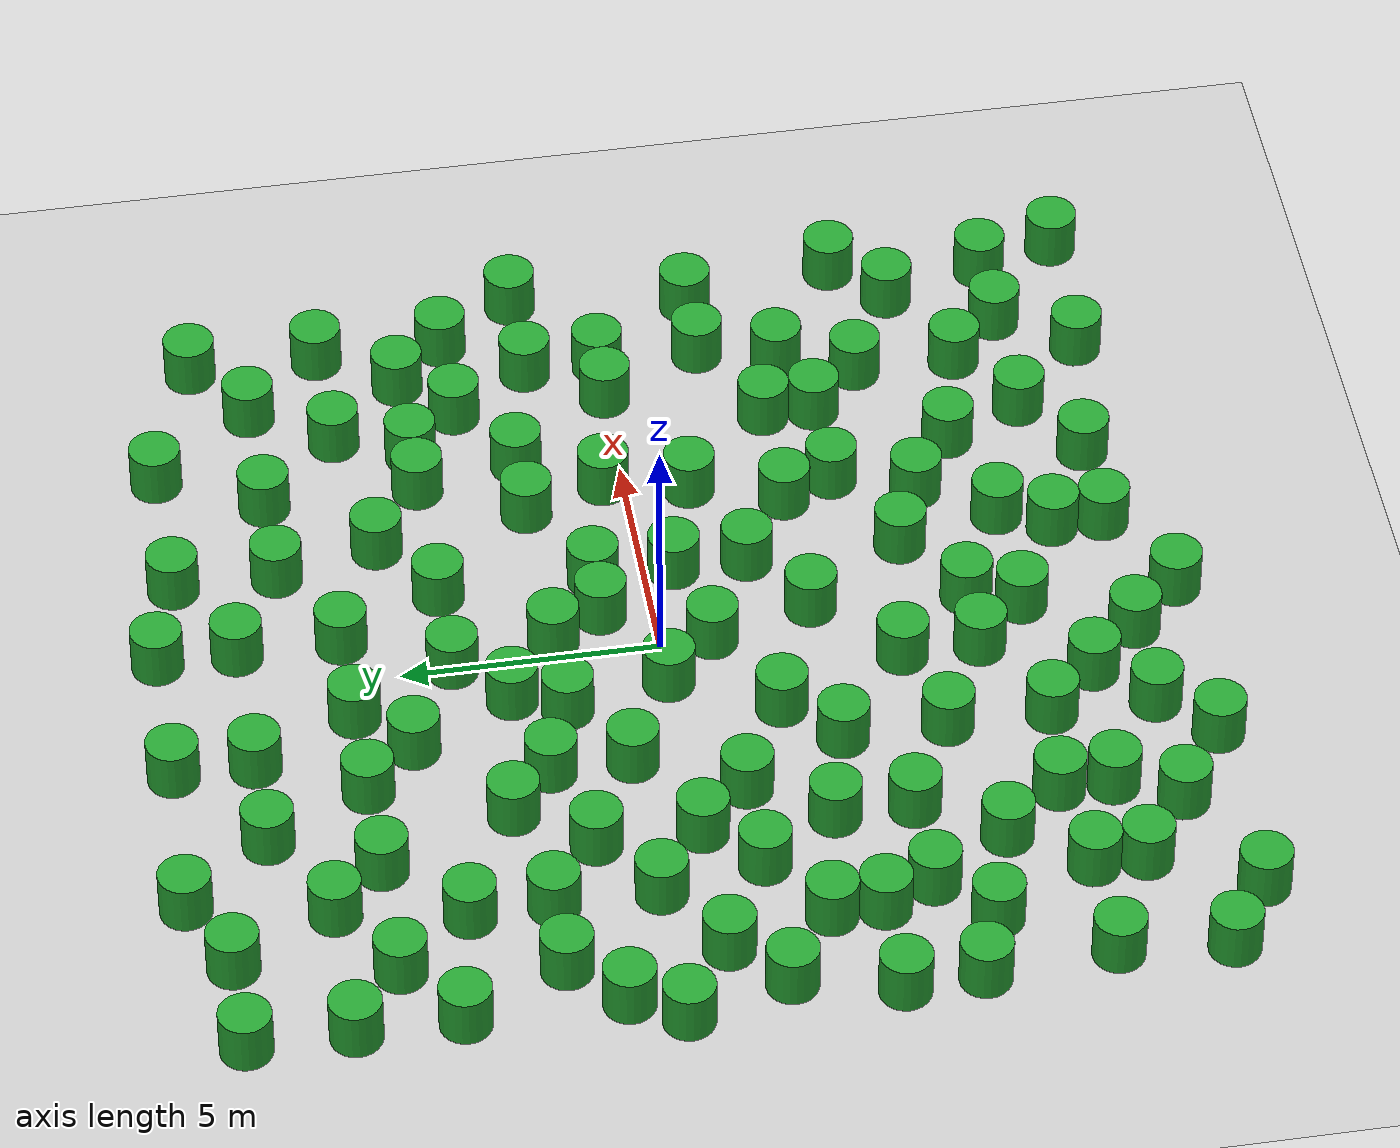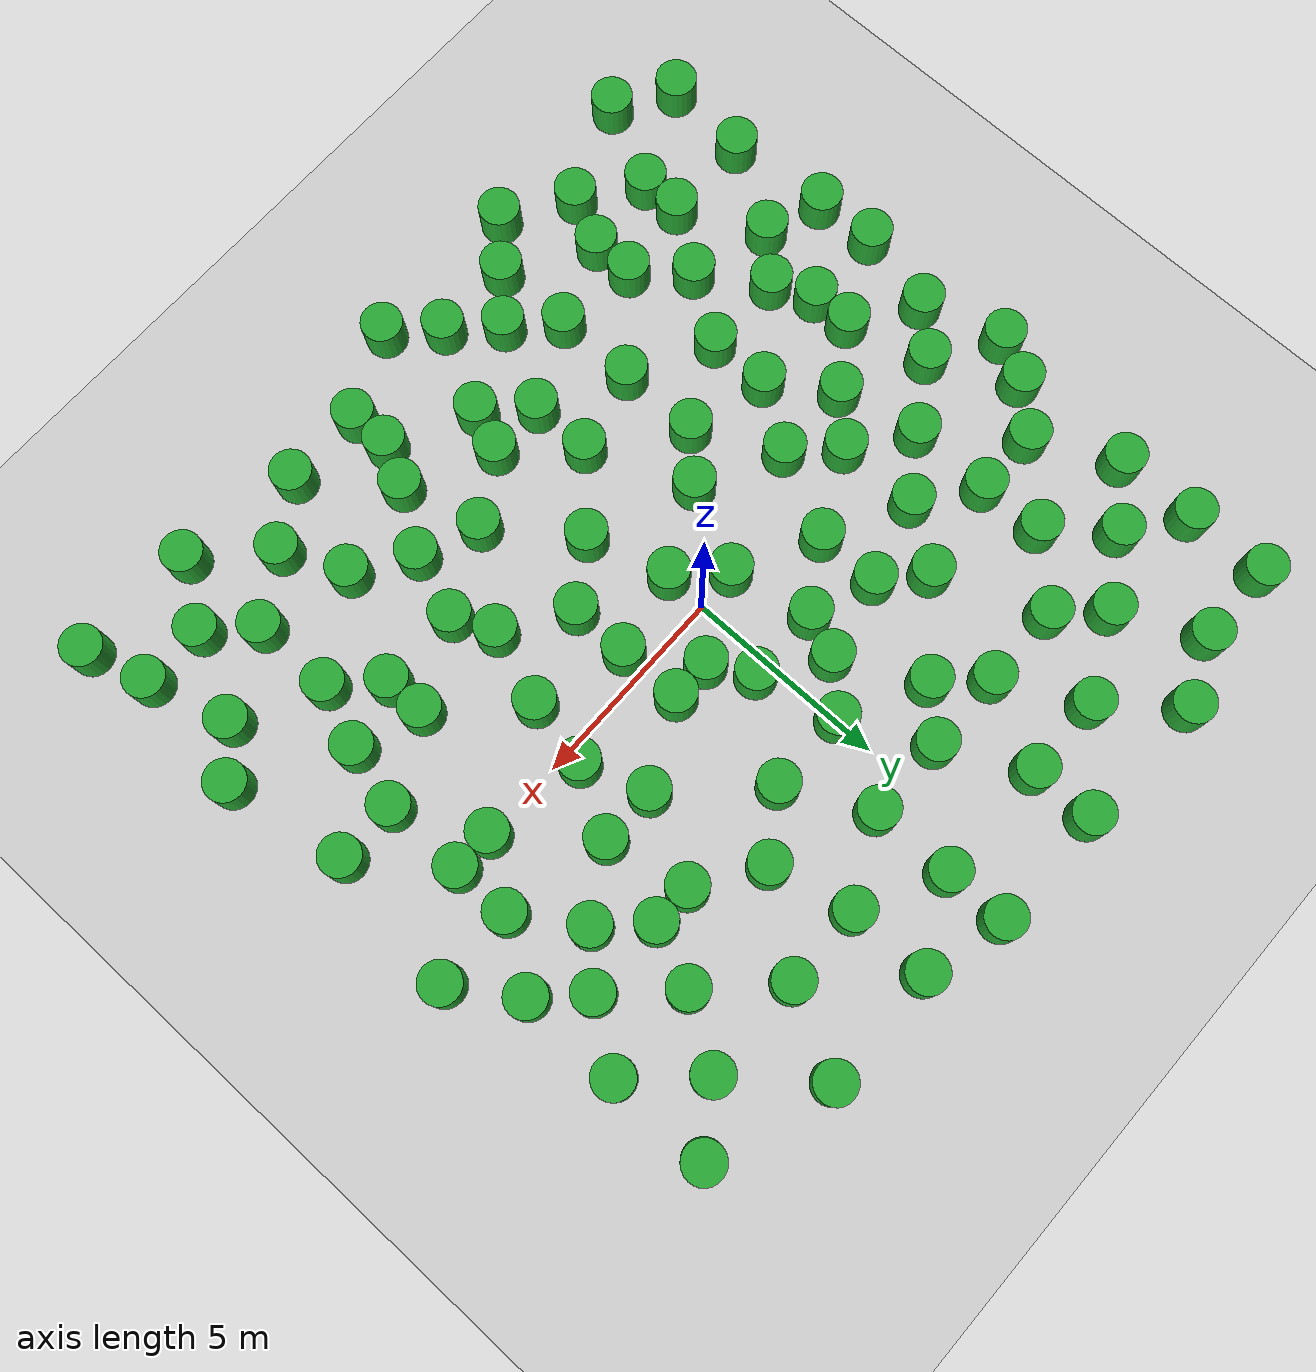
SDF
<sdf version="1.6">
 <world name="default">
  <light name="sun" type="directional">
   <pose>0 0 10 0 -0 0</pose>
   <diffuse>0.8 0.8 0.8 1</diffuse>
   <specular>0.2 0.2 0.2 1</specular>
   <attenuation>
    <range>1000</range>
    <constant>0.9</constant>
    <linear>0.01</linear>
    <quadratic>0.001</quadratic>
   </attenuation>
   <direction>-0.5 0.1 -0.9</direction>
  </light>
  <model name="ground_plane">
   <static>1</static>
   <link name="link">
    <collision name="collision">
     <geometry><plane><normal>0 0 1</normal><size>100 100</size></plane></geometry>
     <surface><friction><ode><mu>100</mu><mu2>50</mu2></ode></friction></surface>
    </collision>
    <visual name="visual">
     <cast_shadows>0</cast_shadows>
     <geometry><plane><normal>0 0 1</normal><size>100 100</size></plane></geometry>
     <material>
      <script><uri>file://media/materials/scripts/gazebo.material</uri><name>Gazebo/Gray</name></script>
     </material>
    </visual>
   </link>
  </model>
  <gravity>0 0 -9.8</gravity>
  <magnetic_field>6e-06 2.3e-05 -4.2e-05</magnetic_field>
  <atmosphere type="adiabatic"/>
  <physics name="default_physics" default="0" type="ode">
   <max_step_size>0.001</max_step_size>
   <real_time_factor>1</real_time_factor>
   <real_time_update_rate>1000</real_time_update_rate>
  </physics>
  <scene><ambient>0.4 0.4 0.4 1</ambient><background>0.7 0.7 0.7 1</background><shadows>1</shadows></scene>
  <spherical_coordinates>
   <surface_model>EARTH_WGS84</surface_model>
   <latitude_deg>0</latitude_deg>
   <longitude_deg>0</longitude_deg>
   <elevation>0</elevation>
   <heading_deg>0</heading_deg>
  </spherical_coordinates>
  <model name="unit_cylinder">
   <pose>-9.39398 -9.14433 0.499994 -3e-06 -1e-06 -0</pose>
   <link name="link">
    <inertial>
     <mass>1</mass>
     <inertia><ixx>0.145833</ixx><ixy>0</ixy><ixz>0</ixz><iyy>0.145833</iyy><iyz>0</iyz><izz>0.125</izz></inertia>
    </inertial>
    <collision name="collision">
     <geometry><cylinder><radius>0.5</radius><length>1</length></cylinder></geometry>
    </collision>
    <visual name="visual">
     <geometry><cylinder><radius>0.5</radius><length>1</length></cylinder></geometry>
     <material>
      <script><name>Gazebo/Green</name><uri>file://media/materials/scripts/gazebo.material</uri></script>
     </material>
    </visual>
   </link>
  </model>
  <model name="unit_cylinder_clone">
   <pose>-9.20038 -7.01612 0.499994 -3e-06 -2e-06 0</pose>
   <link name="link">
    <inertial>
     <mass>1</mass>
     <inertia><ixx>0.145833</ixx><ixy>0</ixy><ixz>0</ixz><iyy>0.145833</iyy><iyz>0</iyz><izz>0.125</izz></inertia>
    </inertial>
    <collision name="collision">
     <geometry><cylinder><radius>0.5</radius><length>1</length></cylinder></geometry>
    </collision>
    <visual name="visual">
     <geometry><cylinder><radius>0.5</radius><length>1</length></cylinder></geometry>
     <material>
      <script><name>Gazebo/Green</name><uri>file://media/materials/scripts/gazebo.material</uri></script>
     </material>
    </visual>
   </link>
  </model>
  <model name="unit_cylinder_clone_0">
   <pose>-8 -5 0.499994 -3e-06 -2e-06 0</pose>
   <link name="link">
    <inertial>
     <mass>1</mass>
     <inertia><ixx>0.145833</ixx><ixy>0</ixy><ixz>0</ixz><iyy>0.145833</iyy><iyz>0</iyz><izz>0.125</izz></inertia>
    </inertial>
    <collision name="collision">
     <geometry><cylinder><radius>0.5</radius><length>1</length></cylinder></geometry>
    </collision>
    <visual name="visual">
     <geometry><cylinder><radius>0.5</radius><length>1</length></cylinder></geometry>
     <material>
      <script><name>Gazebo/Green</name><uri>file://media/materials/scripts/gazebo.material</uri></script>
     </material>
    </visual>
   </link>
  </model>
  <model name="unit_cylinder_clone_1">
   <pose>-7 -7 0.5 0 0 -2e-06</pose>
   <link name="link">
    <inertial>
     <mass>1</mass>
     <inertia><ixx>0.145833</ixx><ixy>0</ixy><ixz>0</ixz><iyy>0.145833</iyy><iyz>0</iyz><izz>0.125</izz></inertia>
    </inertial>
    <collision name="collision">
     <geometry><cylinder><radius>0.5</radius><length>1</length></cylinder></geometry>
    </collision>
    <visual name="visual">
     <geometry><cylinder><radius>0.5</radius><length>1</length></cylinder></geometry>
     <material>
      <script><name>Gazebo/Green</name><uri>file://media/materials/scripts/gazebo.material</uri></script>
     </material>
    </visual>
   </link>
  </model>
  <model name="unit_cylinder_clone_2">
   <pose>-7 -8 0.5 0 -0 -1e-06</pose>
   <link name="link">
    <inertial>
     <mass>1</mass>
     <inertia><ixx>0.145833</ixx><ixy>0</ixy><ixz>0</ixz><iyy>0.145833</iyy><iyz>0</iyz><izz>0.125</izz></inertia>
    </inertial>
    <collision name="collision">
     <geometry><cylinder><radius>0.5</radius><length>1</length></cylinder></geometry>
    </collision>
    <visual name="visual">
     <geometry><cylinder><radius>0.5</radius><length>1</length></cylinder></geometry>
     <material>
      <script><name>Gazebo/Green</name><uri>file://media/materials/scripts/gazebo.material</uri></script>
     </material>
    </visual>
   </link>
  </model>
  <model name="unit_cylinder_clone_3">
   <pose>-5.00002 -7.78309 0.499998 -3e-06 -1e-06 1.1e-05</pose>
   <link name="link">
    <inertial>
     <mass>1</mass>
     <inertia><ixx>0.145833</ixx><ixy>0</ixy><ixz>0</ixz><iyy>0.145833</iyy><iyz>0</iyz><izz>0.125</izz></inertia>
    </inertial>
    <collision name="collision">
     <geometry><cylinder><radius>0.5</radius><length>1</length></cylinder></geometry>
    </collision>
    <visual name="visual">
     <geometry><cylinder><radius>0.5</radius><length>1</length></cylinder></geometry>
     <material>
      <script><name>Gazebo/Green</name><uri>file://media/materials/scripts/gazebo.material</uri></script>
     </material>
    </visual>
   </link>
  </model>
  <model name="unit_cylinder_clone_4">
   <pose>-3 -5 0.499994 -3e-06 -2e-06 0</pose>
   <link name="link">
    <inertial>
     <mass>1</mass>
     <inertia><ixx>0.145833</ixx><ixy>0</ixy><ixz>0</ixz><iyy>0.145833</iyy><iyz>0</iyz><izz>0.125</izz></inertia>
    </inertial>
    <collision name="collision">
     <geometry><cylinder><radius>0.5</radius><length>1</length></cylinder></geometry>
    </collision>
    <visual name="visual">
     <geometry><cylinder><radius>0.5</radius><length>1</length></cylinder></geometry>
     <material>
      <script><name>Gazebo/Green</name><uri>file://media/materials/scripts/gazebo.material</uri></script>
     </material>
    </visual>
   </link>
  </model>
  <model name="unit_cylinder_clone_5">
   <pose>-5 -4 0.499994 -3e-06 -2e-06 0</pose>
   <link name="link">
    <inertial>
     <mass>1</mass>
     <inertia><ixx>0.145833</ixx><ixy>0</ixy><ixz>0</ixz><iyy>0.145833</iyy><iyz>0</iyz><izz>0.125</izz></inertia>
    </inertial>
    <collision name="collision">
     <geometry><cylinder><radius>0.5</radius><length>1</length></cylinder></geometry>
    </collision>
    <visual name="visual">
     <geometry><cylinder><radius>0.5</radius><length>1</length></cylinder></geometry>
     <material>
      <script><name>Gazebo/Green</name><uri>file://media/materials/scripts/gazebo.material</uri></script>
     </material>
    </visual>
   </link>
  </model>
  <model name="unit_cylinder_clone_6">
   <pose>-4 -1 0.499997 3e-06 2e-06 0</pose>
   <link name="link">
    <inertial>
     <mass>1</mass>
     <inertia><ixx>0.145833</ixx><ixy>0</ixy><ixz>0</ixz><iyy>0.145833</iyy><iyz>0</iyz><izz>0.125</izz></inertia>
    </inertial>
    <collision name="collision">
     <geometry><cylinder><radius>0.5</radius><length>1</length></cylinder></geometry>
    </collision>
    <visual name="visual">
     <geometry><cylinder><radius>0.5</radius><length>1</length></cylinder></geometry>
     <material>
      <script><name>Gazebo/Green</name><uri>file://media/materials/scripts/gazebo.material</uri></script>
     </material>
    </visual>
   </link>
  </model>
  <model name="unit_cylinder_clone_7">
   <pose>-6 -1 0.499997 3e-06 2e-06 0</pose>
   <link name="link">
    <inertial>
     <mass>1</mass>
     <inertia><ixx>0.145833</ixx><ixy>0</ixy><ixz>0</ixz><iyy>0.145833</iyy><iyz>0</iyz><izz>0.125</izz></inertia>
    </inertial>
    <collision name="collision">
     <geometry><cylinder><radius>0.5</radius><length>1</length></cylinder></geometry>
    </collision>
    <visual name="visual">
     <geometry><cylinder><radius>0.5</radius><length>1</length></cylinder></geometry>
     <material>
      <script><name>Gazebo/Green</name><uri>file://media/materials/scripts/gazebo.material</uri></script>
     </material>
    </visual>
   </link>
  </model>
  <model name="unit_cylinder_clone_8">
   <pose>-7.45409 -3 0.499994 -3e-06 -2e-06 0</pose>
   <link name="link">
    <inertial>
     <mass>1</mass>
     <inertia><ixx>0.145833</ixx><ixy>0</ixy><ixz>0</ixz><iyy>0.145833</iyy><iyz>0</iyz><izz>0.125</izz></inertia>
    </inertial>
    <collision name="collision">
     <geometry><cylinder><radius>0.5</radius><length>1</length></cylinder></geometry>
    </collision>
    <visual name="visual">
     <geometry><cylinder><radius>0.5</radius><length>1</length></cylinder></geometry>
     <material>
      <script><name>Gazebo/Green</name><uri>file://media/materials/scripts/gazebo.material</uri></script>
     </material>
    </visual>
   </link>
  </model>
  <model name="unit_cylinder_clone_9">
   <pose>-8 -3e-06 0.499997 3e-06 1e-06 -0</pose>
   <link name="link">
    <inertial>
     <mass>1</mass>
     <inertia><ixx>0.145833</ixx><ixy>0</ixy><ixz>0</ixz><iyy>0.145833</iyy><iyz>0</iyz><izz>0.125</izz></inertia>
    </inertial>
    <collision name="collision">
     <geometry><cylinder><radius>0.5</radius><length>1</length></cylinder></geometry>
    </collision>
    <visual name="visual">
     <geometry><cylinder><radius>0.5</radius><length>1</length></cylinder></geometry>
     <material>
      <script><name>Gazebo/Green</name><uri>file://media/materials/scripts/gazebo.material</uri></script>
     </material>
    </visual>
   </link>
  </model>
  <model name="unit_cylinder_clone_10">
   <pose>-6.41645 1 0.499997 3e-06 1e-06 -0</pose>
   <link name="link">
    <inertial>
     <mass>1</mass>
     <inertia><ixx>0.145833</ixx><ixy>0</ixy><ixz>0</ixz><iyy>0.145833</iyy><iyz>0</iyz><izz>0.125</izz></inertia>
    </inertial>
    <collision name="collision">
     <geometry><cylinder><radius>0.5</radius><length>1</length></cylinder></geometry>
    </collision>
    <visual name="visual">
     <geometry><cylinder><radius>0.5</radius><length>1</length></cylinder></geometry>
     <material>
      <script><name>Gazebo/Green</name><uri>file://media/materials/scripts/gazebo.material</uri></script>
     </material>
    </visual>
   </link>
  </model>
  <model name="unit_cylinder_clone_11">
   <pose>-5 2 0.499994 -3e-06 -2e-06 0</pose>
   <link name="link">
    <inertial>
     <mass>1</mass>
     <inertia><ixx>0.145833</ixx><ixy>0</ixy><ixz>0</ixz><iyy>0.145833</iyy><iyz>0</iyz><izz>0.125</izz></inertia>
    </inertial>
    <collision name="collision">
     <geometry><cylinder><radius>0.5</radius><length>1</length></cylinder></geometry>
    </collision>
    <visual name="visual">
     <geometry><cylinder><radius>0.5</radius><length>1</length></cylinder></geometry>
     <material>
      <script><name>Gazebo/Green</name><uri>file://media/materials/scripts/gazebo.material</uri></script>
     </material>
    </visual>
   </link>
  </model>
  <model name="unit_cylinder_clone_12">
   <pose>-3 1 0.499997 3e-06 1e-06 -0</pose>
   <link name="link">
    <inertial>
     <mass>1</mass>
     <inertia><ixx>0.145833</ixx><ixy>0</ixy><ixz>0</ixz><iyy>0.145833</iyy><iyz>0</iyz><izz>0.125</izz></inertia>
    </inertial>
    <collision name="collision">
     <geometry><cylinder><radius>0.5</radius><length>1</length></cylinder></geometry>
    </collision>
    <visual name="visual">
     <geometry><cylinder><radius>0.5</radius><length>1</length></cylinder></geometry>
     <material>
      <script><name>Gazebo/Green</name><uri>file://media/materials/scripts/gazebo.material</uri></script>
     </material>
    </visual>
   </link>
  </model>
  <model name="unit_cylinder_clone_13">
   <pose>-1 -3e-06 0.499996 3e-06 1e-06 -0</pose>
   <link name="link">
    <inertial>
     <mass>1</mass>
     <inertia><ixx>0.145833</ixx><ixy>0</ixy><ixz>0</ixz><iyy>0.145833</iyy><iyz>0</iyz><izz>0.125</izz></inertia>
    </inertial>
    <collision name="collision">
     <geometry><cylinder><radius>0.5</radius><length>1</length></cylinder></geometry>
    </collision>
    <visual name="visual">
     <geometry><cylinder><radius>0.5</radius><length>1</length></cylinder></geometry>
     <material>
      <script><name>Gazebo/Green</name><uri>file://media/materials/scripts/gazebo.material</uri></script>
     </material>
    </visual>
   </link>
  </model>
  <model name="unit_cylinder_clone_14">
   <pose>0.566811 -3 0.499997 3e-06 2e-06 0</pose>
   <link name="link">
    <inertial>
     <mass>1</mass>
     <inertia><ixx>0.145833</ixx><ixy>0</ixy><ixz>0</ixz><iyy>0.145833</iyy><iyz>0</iyz><izz>0.125</izz></inertia>
    </inertial>
    <collision name="collision">
     <geometry><cylinder><radius>0.5</radius><length>1</length></cylinder></geometry>
    </collision>
    <visual name="visual">
     <geometry><cylinder><radius>0.5</radius><length>1</length></cylinder></geometry>
     <material>
      <script><name>Gazebo/Green</name><uri>file://media/materials/scripts/gazebo.material</uri></script>
     </material>
    </visual>
   </link>
  </model>
  <model name="unit_cylinder_clone_15">
   <pose>1e-06 -7 0.499997 3e-06 2e-06 0</pose>
   <link name="link">
    <inertial>
     <mass>1</mass>
     <inertia><ixx>0.145833</ixx><ixy>0</ixy><ixz>0</ixz><iyy>0.145833</iyy><iyz>0</iyz><izz>0.125</izz></inertia>
    </inertial>
    <collision name="collision">
     <geometry><cylinder><radius>0.5</radius><length>1</length></cylinder></geometry>
    </collision>
    <visual name="visual">
     <geometry><cylinder><radius>0.5</radius><length>1</length></cylinder></geometry>
     <material>
      <script><name>Gazebo/Green</name><uri>file://media/materials/scripts/gazebo.material</uri></script>
     </material>
    </visual>
   </link>
  </model>
  <model name="unit_cylinder_clone_16">
   <pose>-2 -8 0.499997 3e-06 2e-06 0</pose>
   <link name="link">
    <inertial>
     <mass>1</mass>
     <inertia><ixx>0.145833</ixx><ixy>0</ixy><ixz>0</ixz><iyy>0.145833</iyy><iyz>0</iyz><izz>0.125</izz></inertia>
    </inertial>
    <collision name="collision">
     <geometry><cylinder><radius>0.5</radius><length>1</length></cylinder></geometry>
    </collision>
    <visual name="visual">
     <geometry><cylinder><radius>0.5</radius><length>1</length></cylinder></geometry>
     <material>
      <script><name>Gazebo/Green</name><uri>file://media/materials/scripts/gazebo.material</uri></script>
     </material>
    </visual>
   </link>
  </model>
  <model name="unit_cylinder_clone_17">
   <pose>2 -9.00001 0.499997 -1e-06 0 -3e-06</pose>
   <link name="link">
    <inertial>
     <mass>1</mass>
     <inertia><ixx>0.145833</ixx><ixy>0</ixy><ixz>0</ixz><iyy>0.145833</iyy><iyz>0</iyz><izz>0.125</izz></inertia>
    </inertial>
    <collision name="collision">
     <geometry><cylinder><radius>0.5</radius><length>1</length></cylinder></geometry>
    </collision>
    <visual name="visual">
     <geometry><cylinder><radius>0.5</radius><length>1</length></cylinder></geometry>
     <material>
      <script><name>Gazebo/Green</name><uri>file://media/materials/scripts/gazebo.material</uri></script>
     </material>
    </visual>
   </link>
  </model>
  <model name="unit_cylinder_clone_18">
   <pose>5.4531 -8 0.499994 -3e-06 -2e-06 0</pose>
   <link name="link">
    <inertial>
     <mass>1</mass>
     <inertia><ixx>0.145833</ixx><ixy>0</ixy><ixz>0</ixz><iyy>0.145833</iyy><iyz>0</iyz><izz>0.125</izz></inertia>
    </inertial>
    <collision name="collision">
     <geometry><cylinder><radius>0.5</radius><length>1</length></cylinder></geometry>
    </collision>
    <visual name="visual">
     <geometry><cylinder><radius>0.5</radius><length>1</length></cylinder></geometry>
     <material>
      <script><name>Gazebo/Green</name><uri>file://media/materials/scripts/gazebo.material</uri></script>
     </material>
    </visual>
   </link>
  </model>
  <model name="unit_cylinder_clone_19">
   <pose>7 -7 0.499997 3e-06 2e-06 0</pose>
   <link name="link">
    <inertial>
     <mass>1</mass>
     <inertia><ixx>0.145833</ixx><ixy>0</ixy><ixz>0</ixz><iyy>0.145833</iyy><iyz>0</iyz><izz>0.125</izz></inertia>
    </inertial>
    <collision name="collision">
     <geometry><cylinder><radius>0.5</radius><length>1</length></cylinder></geometry>
    </collision>
    <visual name="visual">
     <geometry><cylinder><radius>0.5</radius><length>1</length></cylinder></geometry>
     <material>
      <script><name>Gazebo/Green</name><uri>file://media/materials/scripts/gazebo.material</uri></script>
     </material>
    </visual>
   </link>
  </model>
  <model name="unit_cylinder_clone_20">
   <pose>6 -4 0.499997 3e-06 1e-06 -0</pose>
   <link name="link">
    <inertial>
     <mass>1</mass>
     <inertia><ixx>0.145833</ixx><ixy>0</ixy><ixz>0</ixz><iyy>0.145833</iyy><iyz>0</iyz><izz>0.125</izz></inertia>
    </inertial>
    <collision name="collision">
     <geometry><cylinder><radius>0.5</radius><length>1</length></cylinder></geometry>
    </collision>
    <visual name="visual">
     <geometry><cylinder><radius>0.5</radius><length>1</length></cylinder></geometry>
     <material>
      <script><name>Gazebo/Green</name><uri>file://media/materials/scripts/gazebo.material</uri></script>
     </material>
    </visual>
   </link>
  </model>
  <model name="unit_cylinder_clone_21">
   <pose>7.58531 -3.52275 0.499997 3e-06 1e-06 -0</pose>
   <link name="link">
    <inertial>
     <mass>1</mass>
     <inertia><ixx>0.145833</ixx><ixy>0</ixy><ixz>0</ixz><iyy>0.145833</iyy><iyz>0</iyz><izz>0.125</izz></inertia>
    </inertial>
    <collision name="collision">
     <geometry><cylinder><radius>0.5</radius><length>1</length></cylinder></geometry>
    </collision>
    <visual name="visual">
     <geometry><cylinder><radius>0.5</radius><length>1</length></cylinder></geometry>
     <material>
      <script><name>Gazebo/Green</name><uri>file://media/materials/scripts/gazebo.material</uri></script>
     </material>
    </visual>
   </link>
  </model>
  <model name="unit_cylinder_clone_22">
   <pose>7.00001 -0 0.499997 3e-06 2e-06 0</pose>
   <link name="link">
    <inertial>
     <mass>1</mass>
     <inertia><ixx>0.145833</ixx><ixy>0</ixy><ixz>0</ixz><iyy>0.145833</iyy><iyz>0</iyz><izz>0.125</izz></inertia>
    </inertial>
    <collision name="collision">
     <geometry><cylinder><radius>0.5</radius><length>1</length></cylinder></geometry>
    </collision>
    <visual name="visual">
     <geometry><cylinder><radius>0.5</radius><length>1</length></cylinder></geometry>
     <material>
      <script><name>Gazebo/Green</name><uri>file://media/materials/scripts/gazebo.material</uri></script>
     </material>
    </visual>
   </link>
  </model>
  <model name="unit_cylinder_clone_23">
   <pose>8.00001 0 0.5 0 0 -4e-06</pose>
   <link name="link">
    <inertial>
     <mass>1</mass>
     <inertia><ixx>0.145833</ixx><ixy>0</ixy><ixz>0</ixz><iyy>0.145833</iyy><iyz>0</iyz><izz>0.125</izz></inertia>
    </inertial>
    <collision name="collision">
     <geometry><cylinder><radius>0.5</radius><length>1</length></cylinder></geometry>
    </collision>
    <visual name="visual">
     <geometry><cylinder><radius>0.5</radius><length>1</length></cylinder></geometry>
     <material>
      <script><name>Gazebo/Green</name><uri>file://media/materials/scripts/gazebo.material</uri></script>
     </material>
    </visual>
   </link>
  </model>
  <model name="unit_cylinder_clone_24">
   <pose>8 4 0.499997 3e-06 2e-06 0</pose>
   <link name="link">
    <inertial>
     <mass>1</mass>
     <inertia><ixx>0.145833</ixx><ixy>0</ixy><ixz>0</ixz><iyy>0.145833</iyy><iyz>0</iyz><izz>0.125</izz></inertia>
    </inertial>
    <collision name="collision">
     <geometry><cylinder><radius>0.5</radius><length>1</length></cylinder></geometry>
    </collision>
    <visual name="visual">
     <geometry><cylinder><radius>0.5</radius><length>1</length></cylinder></geometry>
     <material>
      <script><name>Gazebo/Green</name><uri>file://media/materials/scripts/gazebo.material</uri></script>
     </material>
    </visual>
   </link>
  </model>
  <model name="unit_cylinder_clone_25">
   <pose>5 4 0.49837 3e-06 2e-06 0</pose>
   <link name="link">
    <inertial>
     <mass>1</mass>
     <inertia><ixx>0.145833</ixx><ixy>0</ixy><ixz>0</ixz><iyy>0.145833</iyy><iyz>0</iyz><izz>0.125</izz></inertia>
    </inertial>
    <collision name="collision">
     <geometry><cylinder><radius>0.5</radius><length>1</length></cylinder></geometry>
    </collision>
    <visual name="visual">
     <geometry><cylinder><radius>0.5</radius><length>1</length></cylinder></geometry>
     <material>
      <script><name>Gazebo/Green</name><uri>file://media/materials/scripts/gazebo.material</uri></script>
     </material>
    </visual>
   </link>
  </model>
  <model name="unit_cylinder_clone_26">
   <pose>4 2 0.499994 -3e-06 -2e-06 0</pose>
   <link name="link">
    <inertial>
     <mass>1</mass>
     <inertia><ixx>0.145833</ixx><ixy>0</ixy><ixz>0</ixz><iyy>0.145833</iyy><iyz>0</iyz><izz>0.125</izz></inertia>
    </inertial>
    <collision name="collision">
     <geometry><cylinder><radius>0.5</radius><length>1</length></cylinder></geometry>
    </collision>
    <visual name="visual">
     <geometry><cylinder><radius>0.5</radius><length>1</length></cylinder></geometry>
     <material>
      <script><name>Gazebo/Green</name><uri>file://media/materials/scripts/gazebo.material</uri></script>
     </material>
    </visual>
   </link>
  </model>
  <model name="unit_cylinder_clone_27">
   <pose>2 4 0.499994 -3e-06 -2e-06 0</pose>
   <link name="link">
    <inertial>
     <mass>1</mass>
     <inertia><ixx>0.145833</ixx><ixy>0</ixy><ixz>0</ixz><iyy>0.145833</iyy><iyz>0</iyz><izz>0.125</izz></inertia>
    </inertial>
    <collision name="collision">
     <geometry><cylinder><radius>0.5</radius><length>1</length></cylinder></geometry>
    </collision>
    <visual name="visual">
     <geometry><cylinder><radius>0.5</radius><length>1</length></cylinder></geometry>
     <material>
      <script><name>Gazebo/Green</name><uri>file://media/materials/scripts/gazebo.material</uri></script>
     </material>
    </visual>
   </link>
  </model>
  <model name="unit_cylinder_clone_28">
   <pose>-2 5 0.499994 -3e-06 -2e-06 0</pose>
   <link name="link">
    <inertial>
     <mass>1</mass>
     <inertia><ixx>0.145833</ixx><ixy>0</ixy><ixz>0</ixz><iyy>0.145833</iyy><iyz>0</iyz><izz>0.125</izz></inertia>
    </inertial>
    <collision name="collision">
     <geometry><cylinder><radius>0.5</radius><length>1</length></cylinder></geometry>
    </collision>
    <visual name="visual">
     <geometry><cylinder><radius>0.5</radius><length>1</length></cylinder></geometry>
     <material>
      <script><name>Gazebo/Green</name><uri>file://media/materials/scripts/gazebo.material</uri></script>
     </material>
    </visual>
   </link>
  </model>
  <model name="unit_cylinder_clone_29">
   <pose>-5 6 0.499997 3e-06 2e-06 0</pose>
   <link name="link">
    <inertial>
     <mass>1</mass>
     <inertia><ixx>0.145833</ixx><ixy>0</ixy><ixz>0</ixz><iyy>0.145833</iyy><iyz>0</iyz><izz>0.125</izz></inertia>
    </inertial>
    <collision name="collision">
     <geometry><cylinder><radius>0.5</radius><length>1</length></cylinder></geometry>
    </collision>
    <visual name="visual">
     <geometry><cylinder><radius>0.5</radius><length>1</length></cylinder></geometry>
     <material>
      <script><name>Gazebo/Green</name><uri>file://media/materials/scripts/gazebo.material</uri></script>
     </material>
    </visual>
   </link>
  </model>
  <model name="unit_cylinder_clone_30">
   <pose>-6.45436 4.56526 0.499997 4e-06 2e-06 -0</pose>
   <link name="link">
    <inertial>
     <mass>1</mass>
     <inertia><ixx>0.145833</ixx><ixy>0</ixy><ixz>0</ixz><iyy>0.145833</iyy><iyz>0</iyz><izz>0.125</izz></inertia>
    </inertial>
    <collision name="collision">
     <geometry><cylinder><radius>0.5</radius><length>1</length></cylinder></geometry>
    </collision>
    <visual name="visual">
     <geometry><cylinder><radius>0.5</radius><length>1</length></cylinder></geometry>
     <material>
      <script><name>Gazebo/Green</name><uri>file://media/materials/scripts/gazebo.material</uri></script>
     </material>
    </visual>
   </link>
  </model>
  <model name="unit_cylinder_clone_31">
   <pose>-7.59942 6 0.499997 3e-06 2e-06 0</pose>
   <link name="link">
    <inertial>
     <mass>1</mass>
     <inertia><ixx>0.145833</ixx><ixy>0</ixy><ixz>0</ixz><iyy>0.145833</iyy><iyz>0</iyz><izz>0.125</izz></inertia>
    </inertial>
    <collision name="collision">
     <geometry><cylinder><radius>0.5</radius><length>1</length></cylinder></geometry>
    </collision>
    <visual name="visual">
     <geometry><cylinder><radius>0.5</radius><length>1</length></cylinder></geometry>
     <material>
      <script><name>Gazebo/Green</name><uri>file://media/materials/scripts/gazebo.material</uri></script>
     </material>
    </visual>
   </link>
  </model>
  <model name="unit_cylinder_clone_32">
   <pose>-2 8 0.499994 -3e-06 -2e-06 0</pose>
   <link name="link">
    <inertial>
     <mass>1</mass>
     <inertia><ixx>0.145833</ixx><ixy>0</ixy><ixz>0</ixz><iyy>0.145833</iyy><iyz>0</iyz><izz>0.125</izz></inertia>
    </inertial>
    <collision name="collision">
     <geometry><cylinder><radius>0.5</radius><length>1</length></cylinder></geometry>
    </collision>
    <visual name="visual">
     <geometry><cylinder><radius>0.5</radius><length>1</length></cylinder></geometry>
     <material>
      <script><name>Gazebo/Green</name><uri>file://media/materials/scripts/gazebo.material</uri></script>
     </material>
    </visual>
   </link>
  </model>
  <model name="unit_cylinder_clone_33">
   <pose>0.999998 8 0.499994 -3e-06 -2e-06 0</pose>
   <link name="link">
    <inertial>
     <mass>1</mass>
     <inertia><ixx>0.145833</ixx><ixy>0</ixy><ixz>0</ixz><iyy>0.145833</iyy><iyz>0</iyz><izz>0.125</izz></inertia>
    </inertial>
    <collision name="collision">
     <geometry><cylinder><radius>0.5</radius><length>1</length></cylinder></geometry>
    </collision>
    <visual name="visual">
     <geometry><cylinder><radius>0.5</radius><length>1</length></cylinder></geometry>
     <material>
      <script><name>Gazebo/Green</name><uri>file://media/materials/scripts/gazebo.material</uri></script>
     </material>
    </visual>
   </link>
  </model>
  <model name="unit_cylinder_clone_34">
   <pose>3 7 0.499994 -3e-06 -2e-06 0</pose>
   <link name="link">
    <inertial>
     <mass>1</mass>
     <inertia><ixx>0.145833</ixx><ixy>0</ixy><ixz>0</ixz><iyy>0.145833</iyy><iyz>0</iyz><izz>0.125</izz></inertia>
    </inertial>
    <collision name="collision">
     <geometry><cylinder><radius>0.5</radius><length>1</length></cylinder></geometry>
    </collision>
    <visual name="visual">
     <geometry><cylinder><radius>0.5</radius><length>1</length></cylinder></geometry>
     <material>
      <script><name>Gazebo/Green</name><uri>file://media/materials/scripts/gazebo.material</uri></script>
     </material>
    </visual>
   </link>
  </model>
  <model name="unit_cylinder_clone_35">
   <pose>5 7 0.499997 4e-06 3e-06 -0</pose>
   <link name="link">
    <inertial>
     <mass>1</mass>
     <inertia><ixx>0.145833</ixx><ixy>0</ixy><ixz>0</ixz><iyy>0.145833</iyy><iyz>0</iyz><izz>0.125</izz></inertia>
    </inertial>
    <collision name="collision">
     <geometry><cylinder><radius>0.5</radius><length>1</length></cylinder></geometry>
    </collision>
    <visual name="visual">
     <geometry><cylinder><radius>0.5</radius><length>1</length></cylinder></geometry>
     <material>
      <script><name>Gazebo/Green</name><uri>file://media/materials/scripts/gazebo.material</uri></script>
     </material>
    </visual>
   </link>
  </model>
  <model name="unit_cylinder_clone_36">
   <pose>7.57121 7 0.499994 -4e-06 -3e-06 -0</pose>
   <link name="link">
    <inertial>
     <mass>1</mass>
     <inertia><ixx>0.145833</ixx><ixy>0</ixy><ixz>0</ixz><iyy>0.145833</iyy><iyz>0</iyz><izz>0.125</izz></inertia>
    </inertial>
    <collision name="collision">
     <geometry><cylinder><radius>0.5</radius><length>1</length></cylinder></geometry>
    </collision>
    <visual name="visual">
     <geometry><cylinder><radius>0.5</radius><length>1</length></cylinder></geometry>
     <material>
      <script><name>Gazebo/Green</name><uri>file://media/materials/scripts/gazebo.material</uri></script>
     </material>
    </visual>
   </link>
  </model>
  <model name="unit_cylinder_clone_37">
   <pose>9 5.48575 0.499997 3e-06 2e-06 0</pose>
   <link name="link">
    <inertial>
     <mass>1</mass>
     <inertia><ixx>0.145833</ixx><ixy>0</ixy><ixz>0</ixz><iyy>0.145833</iyy><iyz>0</iyz><izz>0.125</izz></inertia>
    </inertial>
    <collision name="collision">
     <geometry><cylinder><radius>0.5</radius><length>1</length></cylinder></geometry>
    </collision>
    <visual name="visual">
     <geometry><cylinder><radius>0.5</radius><length>1</length></cylinder></geometry>
     <material>
      <script><name>Gazebo/Green</name><uri>file://media/materials/scripts/gazebo.material</uri></script>
     </material>
    </visual>
   </link>
  </model>
  <model name="unit_cylinder_clone_38">
   <pose>10 1.46428 0.499997 4e-06 3e-06 -0</pose>
   <link name="link">
    <inertial>
     <mass>1</mass>
     <inertia><ixx>0.145833</ixx><ixy>0</ixy><ixz>0</ixz><iyy>0.145833</iyy><iyz>0</iyz><izz>0.125</izz></inertia>
    </inertial>
    <collision name="collision">
     <geometry><cylinder><radius>0.5</radius><length>1</length></cylinder></geometry>
    </collision>
    <visual name="visual">
     <geometry><cylinder><radius>0.5</radius><length>1</length></cylinder></geometry>
     <material>
      <script><name>Gazebo/Green</name><uri>file://media/materials/scripts/gazebo.material</uri></script>
     </material>
    </visual>
   </link>
  </model>
  <model name="unit_cylinder_clone_39">
   <pose>8 1.4506 0.499998 3e-06 4e-06 -0</pose>
   <link name="link">
    <inertial>
     <mass>1</mass>
     <inertia><ixx>0.145833</ixx><ixy>0</ixy><ixz>0</ixz><iyy>0.145833</iyy><iyz>0</iyz><izz>0.125</izz></inertia>
    </inertial>
    <collision name="collision">
     <geometry><cylinder><radius>0.5</radius><length>1</length></cylinder></geometry>
    </collision>
    <visual name="visual">
     <geometry><cylinder><radius>0.5</radius><length>1</length></cylinder></geometry>
     <material>
      <script><name>Gazebo/Green</name><uri>file://media/materials/scripts/gazebo.material</uri></script>
     </material>
    </visual>
   </link>
  </model>
  <model name="unit_cylinder_clone_40">
   <pose>4.53447 0.412107 0.499997 4e-06 3e-06 -0</pose>
   <link name="link">
    <inertial>
     <mass>1</mass>
     <inertia><ixx>0.145833</ixx><ixy>0</ixy><ixz>0</ixz><iyy>0.145833</iyy><iyz>0</iyz><izz>0.125</izz></inertia>
    </inertial>
    <collision name="collision">
     <geometry><cylinder><radius>0.5</radius><length>1</length></cylinder></geometry>
    </collision>
    <visual name="visual">
     <geometry><cylinder><radius>0.5</radius><length>1</length></cylinder></geometry>
     <material>
      <script><name>Gazebo/Green</name><uri>file://media/materials/scripts/gazebo.material</uri></script>
     </material>
    </visual>
   </link>
  </model>
  <model name="unit_cylinder_clone_41">
   <pose>4.19283 -1.22745 0.499997 4e-06 3e-06 -0</pose>
   <link name="link">
    <inertial>
     <mass>1</mass>
     <inertia><ixx>0.145833</ixx><ixy>0</ixy><ixz>0</ixz><iyy>0.145833</iyy><iyz>0</iyz><izz>0.125</izz></inertia>
    </inertial>
    <collision name="collision">
     <geometry><cylinder><radius>0.5</radius><length>1</length></cylinder></geometry>
    </collision>
    <visual name="visual">
     <geometry><cylinder><radius>0.5</radius><length>1</length></cylinder></geometry>
     <material>
      <script><name>Gazebo/Green</name><uri>file://media/materials/scripts/gazebo.material</uri></script>
     </material>
    </visual>
   </link>
  </model>
  <model name="unit_cylinder_clone_42">
   <pose>3.57059 -3 0.499994 -4e-06 -3e-06 -0</pose>
   <link name="link">
    <inertial>
     <mass>1</mass>
     <inertia><ixx>0.145833</ixx><ixy>0</ixy><ixz>0</ixz><iyy>0.145833</iyy><iyz>0</iyz><izz>0.125</izz></inertia>
    </inertial>
    <collision name="collision">
     <geometry><cylinder><radius>0.5</radius><length>1</length></cylinder></geometry>
    </collision>
    <visual name="visual">
     <geometry><cylinder><radius>0.5</radius><length>1</length></cylinder></geometry>
     <material>
      <script><name>Gazebo/Green</name><uri>file://media/materials/scripts/gazebo.material</uri></script>
     </material>
    </visual>
   </link>
  </model>
  <model name="unit_cylinder_clone_43">
   <pose>3.44881 -5.57403 0.499994 -4e-06 -3e-06 -0</pose>
   <link name="link">
    <inertial>
     <mass>1</mass>
     <inertia><ixx>0.145833</ixx><ixy>0</ixy><ixz>0</ixz><iyy>0.145833</iyy><iyz>0</iyz><izz>0.125</izz></inertia>
    </inertial>
    <collision name="collision">
     <geometry><cylinder><radius>0.5</radius><length>1</length></cylinder></geometry>
    </collision>
    <visual name="visual">
     <geometry><cylinder><radius>0.5</radius><length>1</length></cylinder></geometry>
     <material>
      <script><name>Gazebo/Green</name><uri>file://media/materials/scripts/gazebo.material</uri></script>
     </material>
    </visual>
   </link>
  </model>
  <model name="unit_cylinder_clone_44">
   <pose>2 -0.574814 0.499994 -4e-06 -3e-06 -0</pose>
   <link name="link">
    <inertial>
     <mass>1</mass>
     <inertia><ixx>0.145833</ixx><ixy>0</ixy><ixz>0</ixz><iyy>0.145833</iyy><iyz>0</iyz><izz>0.125</izz></inertia>
    </inertial>
    <collision name="collision">
     <geometry><cylinder><radius>0.5</radius><length>1</length></cylinder></geometry>
    </collision>
    <visual name="visual">
     <geometry><cylinder><radius>0.5</radius><length>1</length></cylinder></geometry>
     <material>
      <script><name>Gazebo/Green</name><uri>file://media/materials/scripts/gazebo.material</uri></script>
     </material>
    </visual>
   </link>
  </model>
  <model name="unit_cylinder_clone_45">
   <pose>1 1 0.499996 4e-06 2e-06 -1e-06</pose>
   <link name="link">
    <inertial>
     <mass>1</mass>
     <inertia><ixx>0.145833</ixx><ixy>0</ixy><ixz>0</ixz><iyy>0.145833</iyy><iyz>0</iyz><izz>0.125</izz></inertia>
    </inertial>
    <collision name="collision">
     <geometry><cylinder><radius>0.5</radius><length>1</length></cylinder></geometry>
    </collision>
    <visual name="visual">
     <geometry><cylinder><radius>0.5</radius><length>1</length></cylinder></geometry>
     <material>
      <script><name>Gazebo/Green</name><uri>file://media/materials/scripts/gazebo.material</uri></script>
     </material>
    </visual>
   </link>
  </model>
  <model name="unit_cylinder_clone_46">
   <pose>0.43835 2 0.499997 4e-06 3e-06 -0</pose>
   <link name="link">
    <inertial>
     <mass>1</mass>
     <inertia><ixx>0.145833</ixx><ixy>0</ixy><ixz>0</ixz><iyy>0.145833</iyy><iyz>0</iyz><izz>0.125</izz></inertia>
    </inertial>
    <collision name="collision">
     <geometry><cylinder><radius>0.5</radius><length>1</length></cylinder></geometry>
    </collision>
    <visual name="visual">
     <geometry><cylinder><radius>0.5</radius><length>1</length></cylinder></geometry>
     <material>
      <script><name>Gazebo/Green</name><uri>file://media/materials/scripts/gazebo.material</uri></script>
     </material>
    </visual>
   </link>
  </model>
  <model name="unit_cylinder_clone_47">
   <pose>-1 3 0.499994 -4e-06 -4e-06 -0</pose>
   <link name="link">
    <inertial>
     <mass>1</mass>
     <inertia><ixx>0.145833</ixx><ixy>0</ixy><ixz>0</ixz><iyy>0.145833</iyy><iyz>0</iyz><izz>0.125</izz></inertia>
    </inertial>
    <collision name="collision">
     <geometry><cylinder><radius>0.5</radius><length>1</length></cylinder></geometry>
    </collision>
    <visual name="visual">
     <geometry><cylinder><radius>0.5</radius><length>1</length></cylinder></geometry>
     <material>
      <script><name>Gazebo/Green</name><uri>file://media/materials/scripts/gazebo.material</uri></script>
     </material>
    </visual>
   </link>
  </model>
  <model name="unit_cylinder_clone_48">
   <pose>-4 3.40442 0.499998 3e-06 -2e-06 0</pose>
   <link name="link">
    <inertial>
     <mass>1</mass>
     <inertia><ixx>0.145833</ixx><ixy>0</ixy><ixz>0</ixz><iyy>0.145833</iyy><iyz>0</iyz><izz>0.125</izz></inertia>
    </inertial>
    <collision name="collision">
     <geometry><cylinder><radius>0.5</radius><length>1</length></cylinder></geometry>
    </collision>
    <visual name="visual">
     <geometry><cylinder><radius>0.5</radius><length>1</length></cylinder></geometry>
     <material>
      <script><name>Gazebo/Green</name><uri>file://media/materials/scripts/gazebo.material</uri></script>
     </material>
    </visual>
   </link>
  </model>
  <model name="unit_cylinder_clone_49">
   <pose>-8 3 0.499992 -3e-06 2e-06 0</pose>
   <link name="link">
    <inertial>
     <mass>1</mass>
     <inertia><ixx>0.145833</ixx><ixy>0</ixy><ixz>0</ixz><iyy>0.145833</iyy><iyz>0</iyz><izz>0.125</izz></inertia>
    </inertial>
    <collision name="collision">
     <geometry><cylinder><radius>0.5</radius><length>1</length></cylinder></geometry>
    </collision>
    <visual name="visual">
     <geometry><cylinder><radius>0.5</radius><length>1</length></cylinder></geometry>
     <material>
      <script><name>Gazebo/Green</name><uri>file://media/materials/scripts/gazebo.material</uri></script>
     </material>
    </visual>
   </link>
  </model>
  <model name="unit_cylinder_clone_50">
   <pose>-7 9 0.499998 3e-06 -2e-06 0</pose>
   <link name="link">
    <inertial>
     <mass>1</mass>
     <inertia><ixx>0.145833</ixx><ixy>0</ixy><ixz>0</ixz><iyy>0.145833</iyy><iyz>0</iyz><izz>0.125</izz></inertia>
    </inertial>
    <collision name="collision">
     <geometry><cylinder><radius>0.5</radius><length>1</length></cylinder></geometry>
    </collision>
    <visual name="visual">
     <geometry><cylinder><radius>0.5</radius><length>1</length></cylinder></geometry>
     <material>
      <script><name>Gazebo/Green</name><uri>file://media/materials/scripts/gazebo.material</uri></script>
     </material>
    </visual>
   </link>
  </model>
  <model name="unit_cylinder_clone_51">
   <pose>-5.40133 9.69105 0.499998 3e-06 -2e-06 0</pose>
   <link name="link">
    <inertial>
     <mass>1</mass>
     <inertia><ixx>0.145833</ixx><ixy>0</ixy><ixz>0</ixz><iyy>0.145833</iyy><iyz>0</iyz><izz>0.125</izz></inertia>
    </inertial>
    <collision name="collision">
     <geometry><cylinder><radius>0.5</radius><length>1</length></cylinder></geometry>
    </collision>
    <visual name="visual">
     <geometry><cylinder><radius>0.5</radius><length>1</length></cylinder></geometry>
     <material>
      <script><name>Gazebo/Green</name><uri>file://media/materials/scripts/gazebo.material</uri></script>
     </material>
    </visual>
   </link>
  </model>
  <model name="unit_cylinder_clone_52">
   <pose>-4 8 0.499998 3e-06 4e-06 -0</pose>
   <link name="link">
    <inertial>
     <mass>1</mass>
     <inertia><ixx>0.145833</ixx><ixy>0</ixy><ixz>0</ixz><iyy>0.145833</iyy><iyz>0</iyz><izz>0.125</izz></inertia>
    </inertial>
    <collision name="collision">
     <geometry><cylinder><radius>0.5</radius><length>1</length></cylinder></geometry>
    </collision>
    <visual name="visual">
     <geometry><cylinder><radius>0.5</radius><length>1</length></cylinder></geometry>
     <material>
      <script><name>Gazebo/Green</name><uri>file://media/materials/scripts/gazebo.material</uri></script>
     </material>
    </visual>
   </link>
  </model>
  <model name="unit_cylinder_clone_53">
   <pose>-3 6 0.499998 3e-06 -2e-06 0</pose>
   <link name="link">
    <inertial>
     <mass>1</mass>
     <inertia><ixx>0.145833</ixx><ixy>0</ixy><ixz>0</ixz><iyy>0.145833</iyy><iyz>0</iyz><izz>0.125</izz></inertia>
    </inertial>
    <collision name="collision">
     <geometry><cylinder><radius>0.5</radius><length>1</length></cylinder></geometry>
    </collision>
    <visual name="visual">
     <geometry><cylinder><radius>0.5</radius><length>1</length></cylinder></geometry>
     <material>
      <script><name>Gazebo/Green</name><uri>file://media/materials/scripts/gazebo.material</uri></script>
     </material>
    </visual>
   </link>
  </model>
  <model name="unit_cylinder_clone_54">
   <pose>-1 6 0.499992 -3e-06 -4e-06 -0</pose>
   <link name="link">
    <inertial>
     <mass>1</mass>
     <inertia><ixx>0.145833</ixx><ixy>0</ixy><ixz>0</ixz><iyy>0.145833</iyy><iyz>0</iyz><izz>0.125</izz></inertia>
    </inertial>
    <collision name="collision">
     <geometry><cylinder><radius>0.5</radius><length>1</length></cylinder></geometry>
    </collision>
    <visual name="visual">
     <geometry><cylinder><radius>0.5</radius><length>1</length></cylinder></geometry>
     <material>
      <script><name>Gazebo/Green</name><uri>file://media/materials/scripts/gazebo.material</uri></script>
     </material>
    </visual>
   </link>
  </model>
  <model name="unit_cylinder_clone_55">
   <pose>0.999998 6 0.499992 -3e-06 -4e-06 -0</pose>
   <link name="link">
    <inertial>
     <mass>1</mass>
     <inertia><ixx>0.145833</ixx><ixy>0</ixy><ixz>0</ixz><iyy>0.145833</iyy><iyz>0</iyz><izz>0.125</izz></inertia>
    </inertial>
    <collision name="collision">
     <geometry><cylinder><radius>0.5</radius><length>1</length></cylinder></geometry>
    </collision>
    <visual name="visual">
     <geometry><cylinder><radius>0.5</radius><length>1</length></cylinder></geometry>
     <material>
      <script><name>Gazebo/Green</name><uri>file://media/materials/scripts/gazebo.material</uri></script>
     </material>
    </visual>
   </link>
  </model>
  <model name="unit_cylinder_clone_56">
   <pose>3.46631 5 0.499992 -3e-06 -4e-06 -0</pose>
   <link name="link">
    <inertial>
     <mass>1</mass>
     <inertia><ixx>0.145833</ixx><ixy>0</ixy><ixz>0</ixz><iyy>0.145833</iyy><iyz>0</iyz><izz>0.125</izz></inertia>
    </inertial>
    <collision name="collision">
     <geometry><cylinder><radius>0.5</radius><length>1</length></cylinder></geometry>
    </collision>
    <visual name="visual">
     <geometry><cylinder><radius>0.5</radius><length>1</length></cylinder></geometry>
     <material>
      <script><name>Gazebo/Green</name><uri>file://media/materials/scripts/gazebo.material</uri></script>
     </material>
    </visual>
   </link>
  </model>
  <model name="unit_cylinder_clone_57">
   <pose>6.59197 5.44027 0.499992 -3e-06 2e-06 0</pose>
   <link name="link">
    <inertial>
     <mass>1</mass>
     <inertia><ixx>0.145833</ixx><ixy>0</ixy><ixz>0</ixz><iyy>0.145833</iyy><iyz>0</iyz><izz>0.125</izz></inertia>
    </inertial>
    <collision name="collision">
     <geometry><cylinder><radius>0.5</radius><length>1</length></cylinder></geometry>
    </collision>
    <visual name="visual">
     <geometry><cylinder><radius>0.5</radius><length>1</length></cylinder></geometry>
     <material>
      <script><name>Gazebo/Green</name><uri>file://media/materials/scripts/gazebo.material</uri></script>
     </material>
    </visual>
   </link>
  </model>
  <model name="unit_cylinder_clone_58">
   <pose>9 8 0.499996 3e-06 1e-06 -0</pose>
   <link name="link">
    <inertial>
     <mass>1</mass>
     <inertia><ixx>0.145833</ixx><ixy>0</ixy><ixz>0</ixz><iyy>0.145833</iyy><iyz>0</iyz><izz>0.125</izz></inertia>
    </inertial>
    <collision name="collision">
     <geometry><cylinder><radius>0.5</radius><length>1</length></cylinder></geometry>
    </collision>
    <visual name="visual">
     <geometry><cylinder><radius>0.5</radius><length>1</length></cylinder></geometry>
     <material>
      <script><name>Gazebo/Green</name><uri>file://media/materials/scripts/gazebo.material</uri></script>
     </material>
    </visual>
   </link>
  </model>
  <model name="unit_cylinder_clone_59">
   <pose>6 9 0.499994 -3e-06 -1e-06 -0</pose>
   <link name="link">
    <inertial>
     <mass>1</mass>
     <inertia><ixx>0.145833</ixx><ixy>0</ixy><ixz>0</ixz><iyy>0.145833</iyy><iyz>0</iyz><izz>0.125</izz></inertia>
    </inertial>
    <collision name="collision">
     <geometry><cylinder><radius>0.5</radius><length>1</length></cylinder></geometry>
    </collision>
    <visual name="visual">
     <geometry><cylinder><radius>0.5</radius><length>1</length></cylinder></geometry>
     <material>
      <script><name>Gazebo/Green</name><uri>file://media/materials/scripts/gazebo.material</uri></script>
     </material>
    </visual>
   </link>
  </model>
  <model name="unit_cylinder_clone_60">
   <pose>3 9 0.499994 -3e-06 -1e-06 -0</pose>
   <link name="link">
    <inertial>
     <mass>1</mass>
     <inertia><ixx>0.145833</ixx><ixy>0</ixy><ixz>0</ixz><iyy>0.145833</iyy><iyz>0</iyz><izz>0.125</izz></inertia>
    </inertial>
    <collision name="collision">
     <geometry><cylinder><radius>0.5</radius><length>1</length></cylinder></geometry>
    </collision>
    <visual name="visual">
     <geometry><cylinder><radius>0.5</radius><length>1</length></cylinder></geometry>
     <material>
      <script><name>Gazebo/Green</name><uri>file://media/materials/scripts/gazebo.material</uri></script>
     </material>
    </visual>
   </link>
  </model>
  <model name="unit_cylinder_clone_61">
   <pose>-2 -2 0.499996 3e-06 1e-06 -0</pose>
   <link name="link">
    <inertial>
     <mass>1</mass>
     <inertia><ixx>0.145833</ixx><ixy>0</ixy><ixz>0</ixz><iyy>0.145833</iyy><iyz>0</iyz><izz>0.125</izz></inertia>
    </inertial>
    <collision name="collision">
     <geometry><cylinder><radius>0.5</radius><length>1</length></cylinder></geometry>
    </collision>
    <visual name="visual">
     <geometry><cylinder><radius>0.5</radius><length>1</length></cylinder></geometry>
     <material>
      <script><name>Gazebo/Green</name><uri>file://media/materials/scripts/gazebo.material</uri></script>
     </material>
    </visual>
   </link>
  </model>
  <model name="unit_cylinder_clone_62">
   <pose>-1 -6 0.499994 -3e-06 -1e-06 -0</pose>
   <link name="link">
    <inertial>
     <mass>1</mass>
     <inertia><ixx>0.145833</ixx><ixy>0</ixy><ixz>0</ixz><iyy>0.145833</iyy><iyz>0</iyz><izz>0.125</izz></inertia>
    </inertial>
    <collision name="collision">
     <geometry><cylinder><radius>0.5</radius><length>1</length></cylinder></geometry>
    </collision>
    <visual name="visual">
     <geometry><cylinder><radius>0.5</radius><length>1</length></cylinder></geometry>
     <material>
      <script><name>Gazebo/Green</name><uri>file://media/materials/scripts/gazebo.material</uri></script>
     </material>
    </visual>
   </link>
  </model>
  <model name="unit_cylinder_clone_63">
   <pose>0.406638 -6 0.499994 -4e-06 -4e-06 -0</pose>
   <link name="link">
    <inertial>
     <mass>1</mass>
     <inertia><ixx>0.145833</ixx><ixy>0</ixy><ixz>0</ixz><iyy>0.145833</iyy><iyz>0</iyz><izz>0.125</izz></inertia>
    </inertial>
    <collision name="collision">
     <geometry><cylinder><radius>0.5</radius><length>1</length></cylinder></geometry>
    </collision>
    <visual name="visual">
     <geometry><cylinder><radius>0.5</radius><length>1</length></cylinder></geometry>
     <material>
      <script><name>Gazebo/Green</name><uri>file://media/materials/scripts/gazebo.material</uri></script>
     </material>
    </visual>
   </link>
  </model>
  <model name="unit_cylinder_clone_64">
   <pose>2 -5 0.499998 3e-06 -2e-06 0</pose>
   <link name="link">
    <inertial>
     <mass>1</mass>
     <inertia><ixx>0.145833</ixx><ixy>0</ixy><ixz>0</ixz><iyy>0.145833</iyy><iyz>0</iyz><izz>0.125</izz></inertia>
    </inertial>
    <collision name="collision">
     <geometry><cylinder><radius>0.5</radius><length>1</length></cylinder></geometry>
    </collision>
    <visual name="visual">
     <geometry><cylinder><radius>0.5</radius><length>1</length></cylinder></geometry>
     <material>
      <script><name>Gazebo/Green</name><uri>file://media/materials/scripts/gazebo.material</uri></script>
     </material>
    </visual>
   </link>
  </model>
  <model name="unit_cylinder_clone_65">
   <pose>4 -4 0.499992 -3e-06 2e-06 0</pose>
   <link name="link">
    <inertial>
     <mass>1</mass>
     <inertia><ixx>0.145833</ixx><ixy>0</ixy><ixz>0</ixz><iyy>0.145833</iyy><iyz>0</iyz><izz>0.125</izz></inertia>
    </inertial>
    <collision name="collision">
     <geometry><cylinder><radius>0.5</radius><length>1</length></cylinder></geometry>
    </collision>
    <visual name="visual">
     <geometry><cylinder><radius>0.5</radius><length>1</length></cylinder></geometry>
     <material>
      <script><name>Gazebo/Green</name><uri>file://media/materials/scripts/gazebo.material</uri></script>
     </material>
    </visual>
   </link>
  </model>
  <model name="unit_cylinder_clone_66">
   <pose>6 -3 0.5 0 -0 1e-06</pose>
   <link name="link">
    <inertial>
     <mass>1</mass>
     <inertia><ixx>0.145833</ixx><ixy>0</ixy><ixz>0</ixz><iyy>0.145833</iyy><iyz>0</iyz><izz>0.125</izz></inertia>
    </inertial>
    <collision name="collision">
     <geometry><cylinder><radius>0.5</radius><length>1</length></cylinder></geometry>
    </collision>
    <visual name="visual">
     <geometry><cylinder><radius>0.5</radius><length>1</length></cylinder></geometry>
     <material>
      <script><name>Gazebo/Green</name><uri>file://media/materials/scripts/gazebo.material</uri></script>
     </material>
    </visual>
   </link>
  </model>
  <model name="unit_cylinder_clone_67">
   <pose>8 -2 0.499998 3e-06 -2e-06 0</pose>
   <link name="link">
    <inertial>
     <mass>1</mass>
     <inertia><ixx>0.145833</ixx><ixy>0</ixy><ixz>0</ixz><iyy>0.145833</iyy><iyz>0</iyz><izz>0.125</izz></inertia>
    </inertial>
    <collision name="collision">
     <geometry><cylinder><radius>0.5</radius><length>1</length></cylinder></geometry>
    </collision>
    <visual name="visual">
     <geometry><cylinder><radius>0.5</radius><length>1</length></cylinder></geometry>
     <material>
      <script><name>Gazebo/Green</name><uri>file://media/materials/scripts/gazebo.material</uri></script>
     </material>
    </visual>
   </link>
  </model>
  <model name="unit_cylinder_clone_68">
   <pose>9 -6 0.499992 -3e-06 2e-06 0</pose>
   <link name="link">
    <inertial>
     <mass>1</mass>
     <inertia><ixx>0.145833</ixx><ixy>0</ixy><ixz>0</ixz><iyy>0.145833</iyy><iyz>0</iyz><izz>0.125</izz></inertia>
    </inertial>
    <collision name="collision">
     <geometry><cylinder><radius>0.5</radius><length>1</length></cylinder></geometry>
    </collision>
    <visual name="visual">
     <geometry><cylinder><radius>0.5</radius><length>1</length></cylinder></geometry>
     <material>
      <script><name>Gazebo/Green</name><uri>file://media/materials/scripts/gazebo.material</uri></script>
     </material>
    </visual>
   </link>
  </model>
  <model name="unit_cylinder_clone_69">
   <pose>8 -8 0.499996 4e-06 3e-06 -0</pose>
   <link name="link">
    <inertial>
     <mass>1</mass>
     <inertia><ixx>0.145833</ixx><ixy>0</ixy><ixz>0</ixz><iyy>0.145833</iyy><iyz>0</iyz><izz>0.125</izz></inertia>
    </inertial>
    <collision name="collision">
     <geometry><cylinder><radius>0.5</radius><length>1</length></cylinder></geometry>
    </collision>
    <visual name="visual">
     <geometry><cylinder><radius>0.5</radius><length>1</length></cylinder></geometry>
     <material>
      <script><name>Gazebo/Green</name><uri>file://media/materials/scripts/gazebo.material</uri></script>
     </material>
    </visual>
   </link>
  </model>
  <model name="unit_cylinder_clone_70">
   <pose>2 -8 0.499994 -5e-06 -2e-06 0</pose>
   <link name="link">
    <inertial>
     <mass>1</mass>
     <inertia><ixx>0.145833</ixx><ixy>0</ixy><ixz>0</ixz><iyy>0.145833</iyy><iyz>0</iyz><izz>0.125</izz></inertia>
    </inertial>
    <collision name="collision">
     <geometry><cylinder><radius>0.5</radius><length>1</length></cylinder></geometry>
    </collision>
    <visual name="visual">
     <geometry><cylinder><radius>0.5</radius><length>1</length></cylinder></geometry>
     <material>
      <script><name>Gazebo/Green</name><uri>file://media/materials/scripts/gazebo.material</uri></script>
     </material>
    </visual>
   </link>
  </model>
  <model name="unit_cylinder_clone_71">
   <pose>4.77626 -6.45431 0.499996 4e-06 4e-06 -0</pose>
   <link name="link">
    <inertial>
     <mass>1</mass>
     <inertia><ixx>0.145833</ixx><ixy>0</ixy><ixz>0</ixz><iyy>0.145833</iyy><iyz>0</iyz><izz>0.125</izz></inertia>
    </inertial>
    <collision name="collision">
     <geometry><cylinder><radius>0.5</radius><length>1</length></cylinder></geometry>
    </collision>
    <visual name="visual">
     <geometry><cylinder><radius>0.5</radius><length>1</length></cylinder></geometry>
     <material>
      <script><name>Gazebo/Green</name><uri>file://media/materials/scripts/gazebo.material</uri></script>
     </material>
    </visual>
   </link>
  </model>
  <model name="unit_cylinder_clone_72">
   <pose>2.49725 -7 0.499998 3e-06 -2e-06 0</pose>
   <link name="link">
    <inertial>
     <mass>1</mass>
     <inertia><ixx>0.145833</ixx><ixy>0</ixy><ixz>0</ixz><iyy>0.145833</iyy><iyz>0</iyz><izz>0.125</izz></inertia>
    </inertial>
    <collision name="collision">
     <geometry><cylinder><radius>0.5</radius><length>1</length></cylinder></geometry>
    </collision>
    <visual name="visual">
     <geometry><cylinder><radius>0.5</radius><length>1</length></cylinder></geometry>
     <material>
      <script><name>Gazebo/Green</name><uri>file://media/materials/scripts/gazebo.material</uri></script>
     </material>
    </visual>
   </link>
  </model>
  <model name="unit_cylinder_clone_73">
   <pose>-0.999999 -4.49894 0.499992 -3e-06 2e-06 0</pose>
   <link name="link">
    <inertial>
     <mass>1</mass>
     <inertia><ixx>0.145833</ixx><ixy>0</ixy><ixz>0</ixz><iyy>0.145833</iyy><iyz>0</iyz><izz>0.125</izz></inertia>
    </inertial>
    <collision name="collision">
     <geometry><cylinder><radius>0.5</radius><length>1</length></cylinder></geometry>
    </collision>
    <visual name="visual">
     <geometry><cylinder><radius>0.5</radius><length>1</length></cylinder></geometry>
     <material>
      <script><name>Gazebo/Green</name><uri>file://media/materials/scripts/gazebo.material</uri></script>
     </material>
    </visual>
   </link>
  </model>
  <model name="unit_cylinder_clone_74">
   <pose>-5.00001 -6.74045 0.499997 3e-06 2e-06 9.7e-05</pose>
   <link name="link">
    <inertial>
     <mass>1</mass>
     <inertia><ixx>0.145833</ixx><ixy>0</ixy><ixz>0</ixz><iyy>0.145833</iyy><iyz>0</iyz><izz>0.125</izz></inertia>
    </inertial>
    <collision name="collision">
     <geometry><cylinder><radius>0.5</radius><length>1</length></cylinder></geometry>
    </collision>
    <visual name="visual">
     <geometry><cylinder><radius>0.5</radius><length>1</length></cylinder></geometry>
     <material>
      <script><name>Gazebo/Green</name><uri>file://media/materials/scripts/gazebo.material</uri></script>
     </material>
    </visual>
   </link>
  </model>
  <model name="unit_cylinder_clone_75">
   <pose>-3 -9 0.499993 -3e-06 2e-06 0</pose>
   <link name="link">
    <inertial>
     <mass>1</mass>
     <inertia><ixx>0.145833</ixx><ixy>0</ixy><ixz>0</ixz><iyy>0.145833</iyy><iyz>0</iyz><izz>0.125</izz></inertia>
    </inertial>
    <collision name="collision">
     <geometry><cylinder><radius>0.5</radius><length>1</length></cylinder></geometry>
    </collision>
    <visual name="visual">
     <geometry><cylinder><radius>0.5</radius><length>1</length></cylinder></geometry>
     <material>
      <script><name>Gazebo/Green</name><uri>file://media/materials/scripts/gazebo.material</uri></script>
     </material>
    </visual>
   </link>
  </model>
  <model name="unit_cylinder_clone_76">
   <pose>-3 -7 0.499993 -3e-06 2e-06 0</pose>
   <link name="link">
    <inertial>
     <mass>1</mass>
     <inertia><ixx>0.145833</ixx><ixy>0</ixy><ixz>0</ixz><iyy>0.145833</iyy><iyz>0</iyz><izz>0.125</izz></inertia>
    </inertial>
    <collision name="collision">
     <geometry><cylinder><radius>0.5</radius><length>1</length></cylinder></geometry>
    </collision>
    <visual name="visual">
     <geometry><cylinder><radius>0.5</radius><length>1</length></cylinder></geometry>
     <material>
      <script><name>Gazebo/Green</name><uri>file://media/materials/scripts/gazebo.material</uri></script>
     </material>
    </visual>
   </link>
  </model>
  <model name="unit_cylinder_clone_77">
   <pose>-6 -5.56318 0.499998 3e-06 -2e-06 0</pose>
   <link name="link">
    <inertial>
     <mass>1</mass>
     <inertia><ixx>0.145833</ixx><ixy>0</ixy><ixz>0</ixz><iyy>0.145833</iyy><iyz>0</iyz><izz>0.125</izz></inertia>
    </inertial>
    <collision name="collision">
     <geometry><cylinder><radius>0.5</radius><length>1</length></cylinder></geometry>
    </collision>
    <visual name="visual">
     <geometry><cylinder><radius>0.5</radius><length>1</length></cylinder></geometry>
     <material>
      <script><name>Gazebo/Green</name><uri>file://media/materials/scripts/gazebo.material</uri></script>
     </material>
    </visual>
   </link>
  </model>
  <model name="unit_cylinder_clone_78">
   <pose>-3 -3 0.499994 -4e-06 -1e-06 0</pose>
   <link name="link">
    <inertial>
     <mass>1</mass>
     <inertia><ixx>0.145833</ixx><ixy>0</ixy><ixz>0</ixz><iyy>0.145833</iyy><iyz>0</iyz><izz>0.125</izz></inertia>
    </inertial>
    <collision name="collision">
     <geometry><cylinder><radius>0.5</radius><length>1</length></cylinder></geometry>
    </collision>
    <visual name="visual">
     <geometry><cylinder><radius>0.5</radius><length>1</length></cylinder></geometry>
     <material>
      <script><name>Gazebo/Green</name><uri>file://media/materials/scripts/gazebo.material</uri></script>
     </material>
    </visual>
   </link>
  </model>
  <model name="unit_cylinder_clone_79">
   <pose>-5 -2.49544 0.499993 -4e-06 -1e-06 0</pose>
   <link name="link">
    <inertial>
     <mass>1</mass>
     <inertia><ixx>0.145833</ixx><ixy>0</ixy><ixz>0</ixz><iyy>0.145833</iyy><iyz>0</iyz><izz>0.125</izz></inertia>
    </inertial>
    <collision name="collision">
     <geometry><cylinder><radius>0.5</radius><length>1</length></cylinder></geometry>
    </collision>
    <visual name="visual">
     <geometry><cylinder><radius>0.5</radius><length>1</length></cylinder></geometry>
     <material>
      <script><name>Gazebo/Green</name><uri>file://media/materials/scripts/gazebo.material</uri></script>
     </material>
    </visual>
   </link>
  </model>
  <model name="unit_cylinder_clone_80">
   <pose>-1e-06 -1 0.499998 3e-06 -2e-06 0</pose>
   <link name="link">
    <inertial>
     <mass>1</mass>
     <inertia><ixx>0.145833</ixx><ixy>0</ixy><ixz>0</ixz><iyy>0.145833</iyy><iyz>0</iyz><izz>0.125</izz></inertia>
    </inertial>
    <collision name="collision">
     <geometry><cylinder><radius>0.5</radius><length>1</length></cylinder></geometry>
    </collision>
    <visual name="visual">
     <geometry><cylinder><radius>0.5</radius><length>1</length></cylinder></geometry>
     <material>
      <script><name>Gazebo/Green</name><uri>file://media/materials/scripts/gazebo.material</uri></script>
     </material>
    </visual>
   </link>
  </model>
  <model name="unit_cylinder_clone_81">
   <pose>2 -2 0.499997 4e-06 1e-06 0</pose>
   <link name="link">
    <inertial>
     <mass>1</mass>
     <inertia><ixx>0.145833</ixx><ixy>0</ixy><ixz>0</ixz><iyy>0.145833</iyy><iyz>0</iyz><izz>0.125</izz></inertia>
    </inertial>
    <collision name="collision">
     <geometry><cylinder><radius>0.5</radius><length>1</length></cylinder></geometry>
    </collision>
    <visual name="visual">
     <geometry><cylinder><radius>0.5</radius><length>1</length></cylinder></geometry>
     <material>
      <script><name>Gazebo/Green</name><uri>file://media/materials/scripts/gazebo.material</uri></script>
     </material>
    </visual>
   </link>
  </model>
  <model name="unit_cylinder_clone_82">
   <pose>2 1 0.5 0 0 -2e-06</pose>
   <link name="link">
    <inertial>
     <mass>1</mass>
     <inertia><ixx>0.145833</ixx><ixy>0</ixy><ixz>0</ixz><iyy>0.145833</iyy><iyz>0</iyz><izz>0.125</izz></inertia>
    </inertial>
    <collision name="collision">
     <geometry><cylinder><radius>0.5</radius><length>1</length></cylinder></geometry>
    </collision>
    <visual name="visual">
     <geometry><cylinder><radius>0.5</radius><length>1</length></cylinder></geometry>
     <material>
      <script><name>Gazebo/Green</name><uri>file://media/materials/scripts/gazebo.material</uri></script>
     </material>
    </visual>
   </link>
  </model>
  <model name="unit_cylinder_clone_83">
   <pose>5.40436 2 0.499998 3e-06 -2e-06 0</pose>
   <link name="link">
    <inertial>
     <mass>1</mass>
     <inertia><ixx>0.145833</ixx><ixy>0</ixy><ixz>0</ixz><iyy>0.145833</iyy><iyz>0</iyz><izz>0.125</izz></inertia>
    </inertial>
    <collision name="collision">
     <geometry><cylinder><radius>0.5</radius><length>1</length></cylinder></geometry>
    </collision>
    <visual name="visual">
     <geometry><cylinder><radius>0.5</radius><length>1</length></cylinder></geometry>
     <material>
      <script><name>Gazebo/Green</name><uri>file://media/materials/scripts/gazebo.material</uri></script>
     </material>
    </visual>
   </link>
  </model>
  <model name="unit_cylinder_clone_84">
   <pose>7 3 0.499997 4e-06 2e-06 -0</pose>
   <link name="link">
    <inertial>
     <mass>1</mass>
     <inertia><ixx>0.145833</ixx><ixy>0</ixy><ixz>0</ixz><iyy>0.145833</iyy><iyz>0</iyz><izz>0.125</izz></inertia>
    </inertial>
    <collision name="collision">
     <geometry><cylinder><radius>0.5</radius><length>1</length></cylinder></geometry>
    </collision>
    <visual name="visual">
     <geometry><cylinder><radius>0.5</radius><length>1</length></cylinder></geometry>
     <material>
      <script><name>Gazebo/Green</name><uri>file://media/materials/scripts/gazebo.material</uri></script>
     </material>
    </visual>
   </link>
  </model>
  <model name="unit_cylinder_clone_85">
   <pose>9 3 0.499998 3e-06 -3e-06 0</pose>
   <link name="link">
    <inertial>
     <mass>1</mass>
     <inertia><ixx>0.145833</ixx><ixy>0</ixy><ixz>0</ixz><iyy>0.145833</iyy><iyz>0</iyz><izz>0.125</izz></inertia>
    </inertial>
    <collision name="collision">
     <geometry><cylinder><radius>0.5</radius><length>1</length></cylinder></geometry>
    </collision>
    <visual name="visual">
     <geometry><cylinder><radius>0.5</radius><length>1</length></cylinder></geometry>
     <material>
      <script><name>Gazebo/Green</name><uri>file://media/materials/scripts/gazebo.material</uri></script>
     </material>
    </visual>
   </link>
  </model>
  <model name="unit_cylinder_clone_86">
   <pose>9.49417 -2 0.499998 3e-06 -3e-06 0</pose>
   <link name="link">
    <inertial>
     <mass>1</mass>
     <inertia><ixx>0.145833</ixx><ixy>0</ixy><ixz>0</ixz><iyy>0.145833</iyy><iyz>0</iyz><izz>0.125</izz></inertia>
    </inertial>
    <collision name="collision">
     <geometry><cylinder><radius>0.5</radius><length>1</length></cylinder></geometry>
    </collision>
    <visual name="visual">
     <geometry><cylinder><radius>0.5</radius><length>1</length></cylinder></geometry>
     <material>
      <script><name>Gazebo/Green</name><uri>file://media/materials/scripts/gazebo.material</uri></script>
     </material>
    </visual>
   </link>
  </model>
  <model name="unit_cylinder_clone_87">
   <pose>10 -5 0.499998 3e-06 -3e-06 0</pose>
   <link name="link">
    <inertial>
     <mass>1</mass>
     <inertia><ixx>0.145833</ixx><ixy>0</ixy><ixz>0</ixz><iyy>0.145833</iyy><iyz>0</iyz><izz>0.125</izz></inertia>
    </inertial>
    <collision name="collision">
     <geometry><cylinder><radius>0.5</radius><length>1</length></cylinder></geometry>
    </collision>
    <visual name="visual">
     <geometry><cylinder><radius>0.5</radius><length>1</length></cylinder></geometry>
     <material>
      <script><name>Gazebo/Green</name><uri>file://media/materials/scripts/gazebo.material</uri></script>
     </material>
    </visual>
   </link>
  </model>
  <model name="unit_cylinder_clone_88">
   <pose>7 -5 0.499993 -3e-06 3e-06 0</pose>
   <link name="link">
    <inertial>
     <mass>1</mass>
     <inertia><ixx>0.145833</ixx><ixy>0</ixy><ixz>0</ixz><iyy>0.145833</iyy><iyz>0</iyz><izz>0.125</izz></inertia>
    </inertial>
    <collision name="collision">
     <geometry><cylinder><radius>0.5</radius><length>1</length></cylinder></geometry>
    </collision>
    <visual name="visual">
     <geometry><cylinder><radius>0.5</radius><length>1</length></cylinder></geometry>
     <material>
      <script><name>Gazebo/Green</name><uri>file://media/materials/scripts/gazebo.material</uri></script>
     </material>
    </visual>
   </link>
  </model>
  <model name="unit_cylinder_clone_89">
   <pose>4 -9 0.499997 4e-06 2e-06 -0</pose>
   <link name="link">
    <inertial>
     <mass>1</mass>
     <inertia><ixx>0.145833</ixx><ixy>0</ixy><ixz>0</ixz><iyy>0.145833</iyy><iyz>0</iyz><izz>0.125</izz></inertia>
    </inertial>
    <collision name="collision">
     <geometry><cylinder><radius>0.5</radius><length>1</length></cylinder></geometry>
    </collision>
    <visual name="visual">
     <geometry><cylinder><radius>0.5</radius><length>1</length></cylinder></geometry>
     <material>
      <script><name>Gazebo/Green</name><uri>file://media/materials/scripts/gazebo.material</uri></script>
     </material>
    </visual>
   </link>
  </model>
  <model name="unit_cylinder_clone_90">
   <pose>-0.999999 -9 0.499992 -3e-06 3e-06 0</pose>
   <link name="link">
    <inertial>
     <mass>1</mass>
     <inertia><ixx>0.145833</ixx><ixy>0</ixy><ixz>0</ixz><iyy>0.145833</iyy><iyz>0</iyz><izz>0.125</izz></inertia>
    </inertial>
    <collision name="collision">
     <geometry><cylinder><radius>0.5</radius><length>1</length></cylinder></geometry>
    </collision>
    <visual name="visual">
     <geometry><cylinder><radius>0.5</radius><length>1</length></cylinder></geometry>
     <material>
      <script><name>Gazebo/Green</name><uri>file://media/materials/scripts/gazebo.material</uri></script>
     </material>
    </visual>
   </link>
  </model>
  <model name="unit_cylinder_clone_91">
   <pose>-3 2.55359 0.499992 -3e-06 3e-06 0</pose>
   <link name="link">
    <inertial>
     <mass>1</mass>
     <inertia><ixx>0.145833</ixx><ixy>0</ixy><ixz>0</ixz><iyy>0.145833</iyy><iyz>0</iyz><izz>0.125</izz></inertia>
    </inertial>
    <collision name="collision">
     <geometry><cylinder><radius>0.5</radius><length>1</length></cylinder></geometry>
    </collision>
    <visual name="visual">
     <geometry><cylinder><radius>0.5</radius><length>1</length></cylinder></geometry>
     <material>
      <script><name>Gazebo/Green</name><uri>file://media/materials/scripts/gazebo.material</uri></script>
     </material>
    </visual>
   </link>
  </model>
  <model name="unit_cylinder_clone_92">
   <pose>-6.40438 3 0.499997 3e-06 1e-06 -0</pose>
   <link name="link">
    <inertial>
     <mass>1</mass>
     <inertia><ixx>0.145833</ixx><ixy>0</ixy><ixz>0</ixz><iyy>0.145833</iyy><iyz>0</iyz><izz>0.125</izz></inertia>
    </inertial>
    <collision name="collision">
     <geometry><cylinder><radius>0.5</radius><length>1</length></cylinder></geometry>
    </collision>
    <visual name="visual">
     <geometry><cylinder><radius>0.5</radius><length>1</length></cylinder></geometry>
     <material>
      <script><name>Gazebo/Green</name><uri>file://media/materials/scripts/gazebo.material</uri></script>
     </material>
    </visual>
   </link>
  </model>
  <model name="unit_cylinder_clone_93">
   <pose>-9 2 0.499993 -3e-06 -1e-06 -0</pose>
   <link name="link">
    <inertial>
     <mass>1</mass>
     <inertia><ixx>0.145833</ixx><ixy>0</ixy><ixz>0</ixz><iyy>0.145833</iyy><iyz>0</iyz><izz>0.125</izz></inertia>
    </inertial>
    <collision name="collision">
     <geometry><cylinder><radius>0.5</radius><length>1</length></cylinder></geometry>
    </collision>
    <visual name="visual">
     <geometry><cylinder><radius>0.5</radius><length>1</length></cylinder></geometry>
     <material>
      <script><name>Gazebo/Green</name><uri>file://media/materials/scripts/gazebo.material</uri></script>
     </material>
    </visual>
   </link>
  </model>
  <model name="unit_cylinder_clone_94">
   <pose>-9 5 0.499996 3e-06 1e-06 -0</pose>
   <link name="link">
    <inertial>
     <mass>1</mass>
     <inertia><ixx>0.145833</ixx><ixy>0</ixy><ixz>0</ixz><iyy>0.145833</iyy><iyz>0</iyz><izz>0.125</izz></inertia>
    </inertial>
    <collision name="collision">
     <geometry><cylinder><radius>0.5</radius><length>1</length></cylinder></geometry>
    </collision>
    <visual name="visual">
     <geometry><cylinder><radius>0.5</radius><length>1</length></cylinder></geometry>
     <material>
      <script><name>Gazebo/Green</name><uri>file://media/materials/scripts/gazebo.material</uri></script>
     </material>
    </visual>
   </link>
  </model>
  <model name="unit_cylinder_clone_95">
   <pose>-9 7 0.499992 -3e-06 3e-06 0</pose>
   <link name="link">
    <inertial>
     <mass>1</mass>
     <inertia><ixx>0.145833</ixx><ixy>0</ixy><ixz>0</ixz><iyy>0.145833</iyy><iyz>0</iyz><izz>0.125</izz></inertia>
    </inertial>
    <collision name="collision">
     <geometry><cylinder><radius>0.5</radius><length>1</length></cylinder></geometry>
    </collision>
    <visual name="visual">
     <geometry><cylinder><radius>0.5</radius><length>1</length></cylinder></geometry>
     <material>
      <script><name>Gazebo/Green</name><uri>file://media/materials/scripts/gazebo.material</uri></script>
     </material>
    </visual>
   </link>
  </model>
  <model name="unit_cylinder_clone_96">
   <pose>-9 9 0.499996 3e-06 1e-06 -0</pose>
   <link name="link">
    <inertial>
     <mass>1</mass>
     <inertia><ixx>0.145833</ixx><ixy>0</ixy><ixz>0</ixz><iyy>0.145833</iyy><iyz>0</iyz><izz>0.125</izz></inertia>
    </inertial>
    <collision name="collision">
     <geometry><cylinder><radius>0.5</radius><length>1</length></cylinder></geometry>
    </collision>
    <visual name="visual">
     <geometry><cylinder><radius>0.5</radius><length>1</length></cylinder></geometry>
     <material>
      <script><name>Gazebo/Green</name><uri>file://media/materials/scripts/gazebo.material</uri></script>
     </material>
    </visual>
   </link>
  </model>
  <model name="unit_cylinder_clone_97">
   <pose>-6 7 0.499998 3e-06 -3e-06 0</pose>
   <link name="link">
    <inertial>
     <mass>1</mass>
     <inertia><ixx>0.145833</ixx><ixy>0</ixy><ixz>0</ixz><iyy>0.145833</iyy><iyz>0</iyz><izz>0.125</izz></inertia>
    </inertial>
    <collision name="collision">
     <geometry><cylinder><radius>0.5</radius><length>1</length></cylinder></geometry>
    </collision>
    <visual name="visual">
     <geometry><cylinder><radius>0.5</radius><length>1</length></cylinder></geometry>
     <material>
      <script><name>Gazebo/Green</name><uri>file://media/materials/scripts/gazebo.material</uri></script>
     </material>
    </visual>
   </link>
  </model>
  <model name="unit_cylinder_clone_98">
   <pose>-2 9.54563 0.499997 3e-06 1e-06 -0</pose>
   <link name="link">
    <inertial>
     <mass>1</mass>
     <inertia><ixx>0.145833</ixx><ixy>0</ixy><ixz>0</ixz><iyy>0.145833</iyy><iyz>0</iyz><izz>0.125</izz></inertia>
    </inertial>
    <collision name="collision">
     <geometry><cylinder><radius>0.5</radius><length>1</length></cylinder></geometry>
    </collision>
    <visual name="visual">
     <geometry><cylinder><radius>0.5</radius><length>1</length></cylinder></geometry>
     <material>
      <script><name>Gazebo/Green</name><uri>file://media/materials/scripts/gazebo.material</uri></script>
     </material>
    </visual>
   </link>
  </model>
  <model name="unit_cylinder_clone_99">
   <pose>0.999998 9.51886 0.499993 -3e-06 -1e-06 -0</pose>
   <link name="link">
    <inertial>
     <mass>1</mass>
     <inertia><ixx>0.145833</ixx><ixy>0</ixy><ixz>0</ixz><iyy>0.145833</iyy><iyz>0</iyz><izz>0.125</izz></inertia>
    </inertial>
    <collision name="collision">
     <geometry><cylinder><radius>0.5</radius><length>1</length></cylinder></geometry>
    </collision>
    <visual name="visual">
     <geometry><cylinder><radius>0.5</radius><length>1</length></cylinder></geometry>
     <material>
      <script><name>Gazebo/Green</name><uri>file://media/materials/scripts/gazebo.material</uri></script>
     </material>
    </visual>
   </link>
  </model>
  <model name="unit_cylinder_clone_100">
   <pose>2e-06 4 0.499992 -3e-06 4e-06 0</pose>
   <link name="link">
    <inertial>
     <mass>1</mass>
     <inertia><ixx>0.145833</ixx><ixy>0</ixy><ixz>0</ixz><iyy>0.145833</iyy><iyz>0</iyz><izz>0.125</izz></inertia>
    </inertial>
    <collision name="collision">
     <geometry><cylinder><radius>0.5</radius><length>1</length></cylinder></geometry>
    </collision>
    <visual name="visual">
     <geometry><cylinder><radius>0.5</radius><length>1</length></cylinder></geometry>
     <material>
      <script><name>Gazebo/Green</name><uri>file://media/materials/scripts/gazebo.material</uri></script>
     </material>
    </visual>
   </link>
  </model>
  <model name="unit_cylinder_clone_101">
   <pose>-9 -0.999999 0.499992 -3e-06 4e-06 0</pose>
   <link name="link">
    <inertial>
     <mass>1</mass>
     <inertia><ixx>0.145833</ixx><ixy>0</ixy><ixz>0</ixz><iyy>0.145833</iyy><iyz>0</iyz><izz>0.125</izz></inertia>
    </inertial>
    <collision name="collision">
     <geometry><cylinder><radius>0.5</radius><length>1</length></cylinder></geometry>
    </collision>
    <visual name="visual">
     <geometry><cylinder><radius>0.5</radius><length>1</length></cylinder></geometry>
     <material>
      <script><name>Gazebo/Green</name><uri>file://media/materials/scripts/gazebo.material</uri></script>
     </material>
    </visual>
   </link>
  </model>
  <model name="unit_cylinder_clone_102">
   <pose>-9.48421 -3 0.499992 -3e-06 4e-06 0</pose>
   <link name="link">
    <inertial>
     <mass>1</mass>
     <inertia><ixx>0.145833</ixx><ixy>0</ixy><ixz>0</ixz><iyy>0.145833</iyy><iyz>0</iyz><izz>0.125</izz></inertia>
    </inertial>
    <collision name="collision">
     <geometry><cylinder><radius>0.5</radius><length>1</length></cylinder></geometry>
    </collision>
    <visual name="visual">
     <geometry><cylinder><radius>0.5</radius><length>1</length></cylinder></geometry>
     <material>
      <script><name>Gazebo/Green</name><uri>file://media/materials/scripts/gazebo.material</uri></script>
     </material>
    </visual>
   </link>
  </model>
  <model name="unit_cylinder_clone_103">
   <pose>-9.41675 -4.4994 0.499992 -3e-06 4e-06 0</pose>
   <link name="link">
    <inertial>
     <mass>1</mass>
     <inertia><ixx>0.145833</ixx><ixy>0</ixy><ixz>0</ixz><iyy>0.145833</iyy><iyz>0</iyz><izz>0.125</izz></inertia>
    </inertial>
    <collision name="collision">
     <geometry><cylinder><radius>0.5</radius><length>1</length></cylinder></geometry>
    </collision>
    <visual name="visual">
     <geometry><cylinder><radius>0.5</radius><length>1</length></cylinder></geometry>
     <material>
      <script><name>Gazebo/Green</name><uri>file://media/materials/scripts/gazebo.material</uri></script>
     </material>
    </visual>
   </link>
  </model>
  <model name="unit_cylinder_clone_104">
   <pose>-5.59005 -9 0.499992 -3e-06 4e-06 0</pose>
   <link name="link">
    <inertial>
     <mass>1</mass>
     <inertia><ixx>0.145833</ixx><ixy>0</ixy><ixz>0</ixz><iyy>0.145833</iyy><iyz>0</iyz><izz>0.125</izz></inertia>
    </inertial>
    <collision name="collision">
     <geometry><cylinder><radius>0.5</radius><length>1</length></cylinder></geometry>
    </collision>
    <visual name="visual">
     <geometry><cylinder><radius>0.5</radius><length>1</length></cylinder></geometry>
     <material>
      <script><name>Gazebo/Green</name><uri>file://media/materials/scripts/gazebo.material</uri></script>
     </material>
    </visual>
   </link>
  </model>
  <model name="unit_cylinder_clone_105">
   <pose>-8 -10 0.499998 3e-06 -4e-06 0</pose>
   <link name="link">
    <inertial>
     <mass>1</mass>
     <inertia><ixx>0.145833</ixx><ixy>0</ixy><ixz>0</ixz><iyy>0.145833</iyy><iyz>0</iyz><izz>0.125</izz></inertia>
    </inertial>
    <collision name="collision">
     <geometry><cylinder><radius>0.5</radius><length>1</length></cylinder></geometry>
    </collision>
    <visual name="visual">
     <geometry><cylinder><radius>0.5</radius><length>1</length></cylinder></geometry>
     <material>
      <script><name>Gazebo/Green</name><uri>file://media/materials/scripts/gazebo.material</uri></script>
     </material>
    </visual>
   </link>
  </model>
  <model name="unit_cylinder_clone_106">
   <pose>10 -9.55018 0.499992 -3e-06 4e-06 0</pose>
   <link name="link">
    <inertial>
     <mass>1</mass>
     <inertia><ixx>0.145833</ixx><ixy>0</ixy><ixz>0</ixz><iyy>0.145833</iyy><iyz>0</iyz><izz>0.125</izz></inertia>
    </inertial>
    <collision name="collision">
     <geometry><cylinder><radius>0.5</radius><length>1</length></cylinder></geometry>
    </collision>
    <visual name="visual">
     <geometry><cylinder><radius>0.5</radius><length>1</length></cylinder></geometry>
     <material>
      <script><name>Gazebo/Green</name><uri>file://media/materials/scripts/gazebo.material</uri></script>
     </material>
    </visual>
   </link>
  </model>
  <model name="unit_cylinder_clone_107">
   <pose>9.56897 -8 0.499993 -3e-06 -2e-06 0</pose>
   <link name="link">
    <inertial>
     <mass>1</mass>
     <inertia><ixx>0.145833</ixx><ixy>0</ixy><ixz>0</ixz><iyy>0.145833</iyy><iyz>0</iyz><izz>0.125</izz></inertia>
    </inertial>
    <collision name="collision">
     <geometry><cylinder><radius>0.5</radius><length>1</length></cylinder></geometry>
    </collision>
    <visual name="visual">
     <geometry><cylinder><radius>0.5</radius><length>1</length></cylinder></geometry>
     <material>
      <script><name>Gazebo/Green</name><uri>file://media/materials/scripts/gazebo.material</uri></script>
     </material>
    </visual>
   </link>
  </model>
  <model name="unit_cylinder_clone_108">
   <pose>7 -9.46445 0.499993 -3e-06 -2e-06 0</pose>
   <link name="link">
    <inertial>
     <mass>1</mass>
     <inertia><ixx>0.145833</ixx><ixy>0</ixy><ixz>0</ixz><iyy>0.145833</iyy><iyz>0</iyz><izz>0.125</izz></inertia>
    </inertial>
    <collision name="collision">
     <geometry><cylinder><radius>0.5</radius><length>1</length></cylinder></geometry>
    </collision>
    <visual name="visual">
     <geometry><cylinder><radius>0.5</radius><length>1</length></cylinder></geometry>
     <material>
      <script><name>Gazebo/Green</name><uri>file://media/materials/scripts/gazebo.material</uri></script>
     </material>
    </visual>
   </link>
  </model>
  <model name="unit_cylinder_clone_109">
   <pose>2e-06 -10 0.499998 4e-06 4e-06 -0</pose>
   <link name="link">
    <inertial>
     <mass>1</mass>
     <inertia><ixx>0.145833</ixx><ixy>0</ixy><ixz>0</ixz><iyy>0.145833</iyy><iyz>0</iyz><izz>0.125</izz></inertia>
    </inertial>
    <collision name="collision">
     <geometry><cylinder><radius>0.5</radius><length>1</length></cylinder></geometry>
    </collision>
    <visual name="visual">
     <geometry><cylinder><radius>0.5</radius><length>1</length></cylinder></geometry>
     <material>
      <script><name>Gazebo/Green</name><uri>file://media/materials/scripts/gazebo.material</uri></script>
     </material>
    </visual>
   </link>
  </model>
  <model name="unit_cylinder_clone_110">
   <pose>-4 -10 0.499993 -3e-06 -3e-06 0</pose>
   <link name="link">
    <inertial>
     <mass>1</mass>
     <inertia><ixx>0.145833</ixx><ixy>0</ixy><ixz>0</ixz><iyy>0.145833</iyy><iyz>0</iyz><izz>0.125</izz></inertia>
    </inertial>
    <collision name="collision">
     <geometry><cylinder><radius>0.5</radius><length>1</length></cylinder></geometry>
    </collision>
    <visual name="visual">
     <geometry><cylinder><radius>0.5</radius><length>1</length></cylinder></geometry>
     <material>
      <script><name>Gazebo/Green</name><uri>file://media/materials/scripts/gazebo.material</uri></script>
     </material>
    </visual>
   </link>
  </model>
  <model name="unit_cylinder_clone_111">
   <pose>-1.42352 2 0.499997 3e-06 4e-06 -0</pose>
   <link name="link">
    <inertial>
     <mass>1</mass>
     <inertia><ixx>0.145833</ixx><ixy>0</ixy><ixz>0</ixz><iyy>0.145833</iyy><iyz>0</iyz><izz>0.125</izz></inertia>
    </inertial>
    <collision name="collision">
     <geometry><cylinder><radius>0.5</radius><length>1</length></cylinder></geometry>
    </collision>
    <visual name="visual">
     <geometry><cylinder><radius>0.5</radius><length>1</length></cylinder></geometry>
     <material>
      <script><name>Gazebo/Green</name><uri>file://media/materials/scripts/gazebo.material</uri></script>
     </material>
    </visual>
   </link>
  </model>
  <model name="unit_cylinder_clone_112">
   <pose>-5 2e-06 0.499993 -3e-06 -4e-06 -0</pose>
   <link name="link">
    <inertial>
     <mass>1</mass>
     <inertia><ixx>0.145833</ixx><ixy>0</ixy><ixz>0</ixz><iyy>0.145833</iyy><iyz>0</iyz><izz>0.125</izz></inertia>
    </inertial>
    <collision name="collision">
     <geometry><cylinder><radius>0.5</radius><length>1</length></cylinder></geometry>
    </collision>
    <visual name="visual">
     <geometry><cylinder><radius>0.5</radius><length>1</length></cylinder></geometry>
     <material>
      <script><name>Gazebo/Green</name><uri>file://media/materials/scripts/gazebo.material</uri></script>
     </material>
    </visual>
   </link>
  </model>
  <model name="unit_cylinder_clone_113">
   <pose>-9.57853 0.999997 0.499996 3e-06 2e-06 0</pose>
   <link name="link">
    <inertial>
     <mass>1</mass>
     <inertia><ixx>0.145833</ixx><ixy>0</ixy><ixz>0</ixz><iyy>0.145833</iyy><iyz>0</iyz><izz>0.125</izz></inertia>
    </inertial>
    <collision name="collision">
     <geometry><cylinder><radius>0.5</radius><length>1</length></cylinder></geometry>
    </collision>
    <visual name="visual">
     <geometry><cylinder><radius>0.5</radius><length>1</length></cylinder></geometry>
     <material>
      <script><name>Gazebo/Green</name><uri>file://media/materials/scripts/gazebo.material</uri></script>
     </material>
    </visual>
   </link>
  </model>
  <model name="unit_cylinder_clone_114">
   <pose>-7.45672 -2 0.498373 0 -0 0</pose>
   <link name="link">
    <inertial>
     <mass>1</mass>
     <inertia><ixx>0.145833</ixx><ixy>0</ixy><ixz>0</ixz><iyy>0.145833</iyy><iyz>0</iyz><izz>0.125</izz></inertia>
    </inertial>
    <collision name="collision">
     <geometry><cylinder><radius>0.5</radius><length>1</length></cylinder></geometry>
    </collision>
    <visual name="visual">
     <geometry><cylinder><radius>0.5</radius><length>1</length></cylinder></geometry>
     <material>
      <script><name>Gazebo/Green</name><uri>file://media/materials/scripts/gazebo.material</uri></script>
     </material>
    </visual>
   </link>
  </model>
  <model name="unit_cylinder_clone_115">
   <pose>-7 -4 0.499993 -3e-06 -4e-06 -0</pose>
   <link name="link">
    <inertial>
     <mass>1</mass>
     <inertia><ixx>0.145833</ixx><ixy>0</ixy><ixz>0</ixz><iyy>0.145833</iyy><iyz>0</iyz><izz>0.125</izz></inertia>
    </inertial>
    <collision name="collision">
     <geometry><cylinder><radius>0.5</radius><length>1</length></cylinder></geometry>
    </collision>
    <visual name="visual">
     <geometry><cylinder><radius>0.5</radius><length>1</length></cylinder></geometry>
     <material>
      <script><name>Gazebo/Green</name><uri>file://media/materials/scripts/gazebo.material</uri></script>
     </material>
    </visual>
   </link>
  </model>
  <model name="unit_cylinder_clone_116">
   <pose>6 4 0.499997 3e-06 4e-06 -0</pose>
   <link name="link">
    <inertial>
     <mass>1</mass>
     <inertia><ixx>0.145833</ixx><ixy>0</ixy><ixz>0</ixz><iyy>0.145833</iyy><iyz>0</iyz><izz>0.125</izz></inertia>
    </inertial>
    <collision name="collision">
     <geometry><cylinder><radius>0.5</radius><length>1</length></cylinder></geometry>
    </collision>
    <visual name="visual">
     <geometry><cylinder><radius>0.5</radius><length>1</length></cylinder></geometry>
     <material>
      <script><name>Gazebo/Green</name><uri>file://media/materials/scripts/gazebo.material</uri></script>
     </material>
    </visual>
   </link>
  </model>
 </world>
</sdf>
